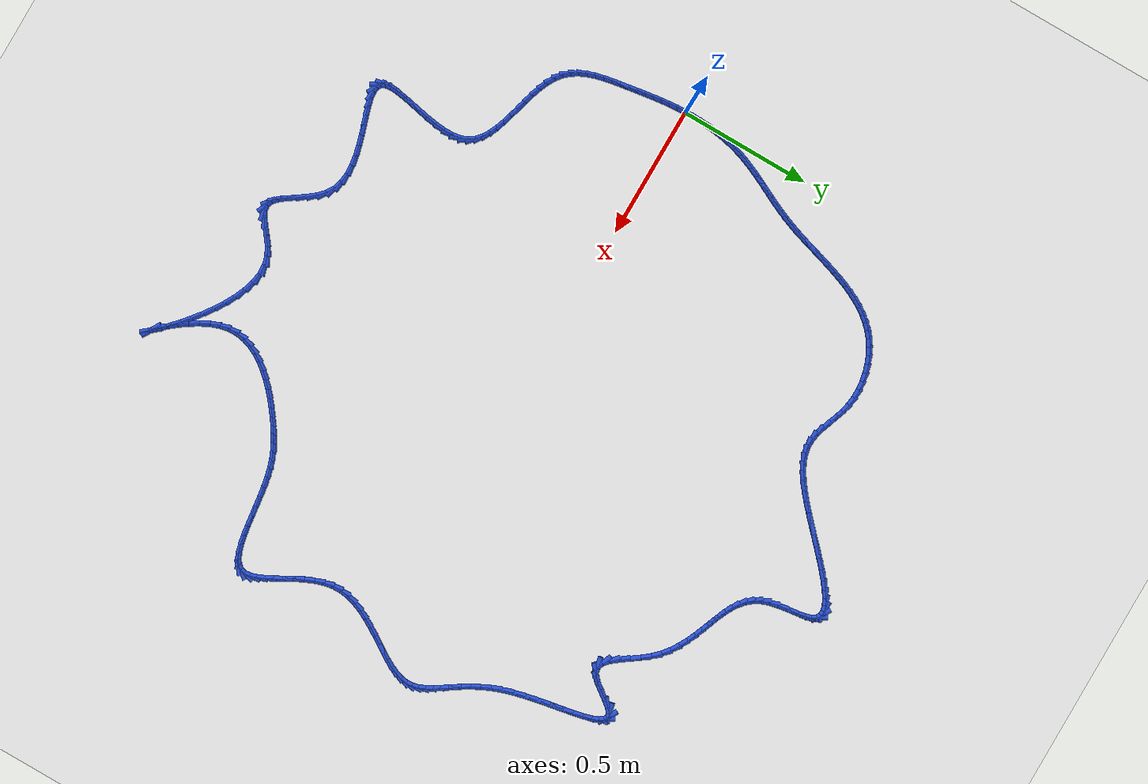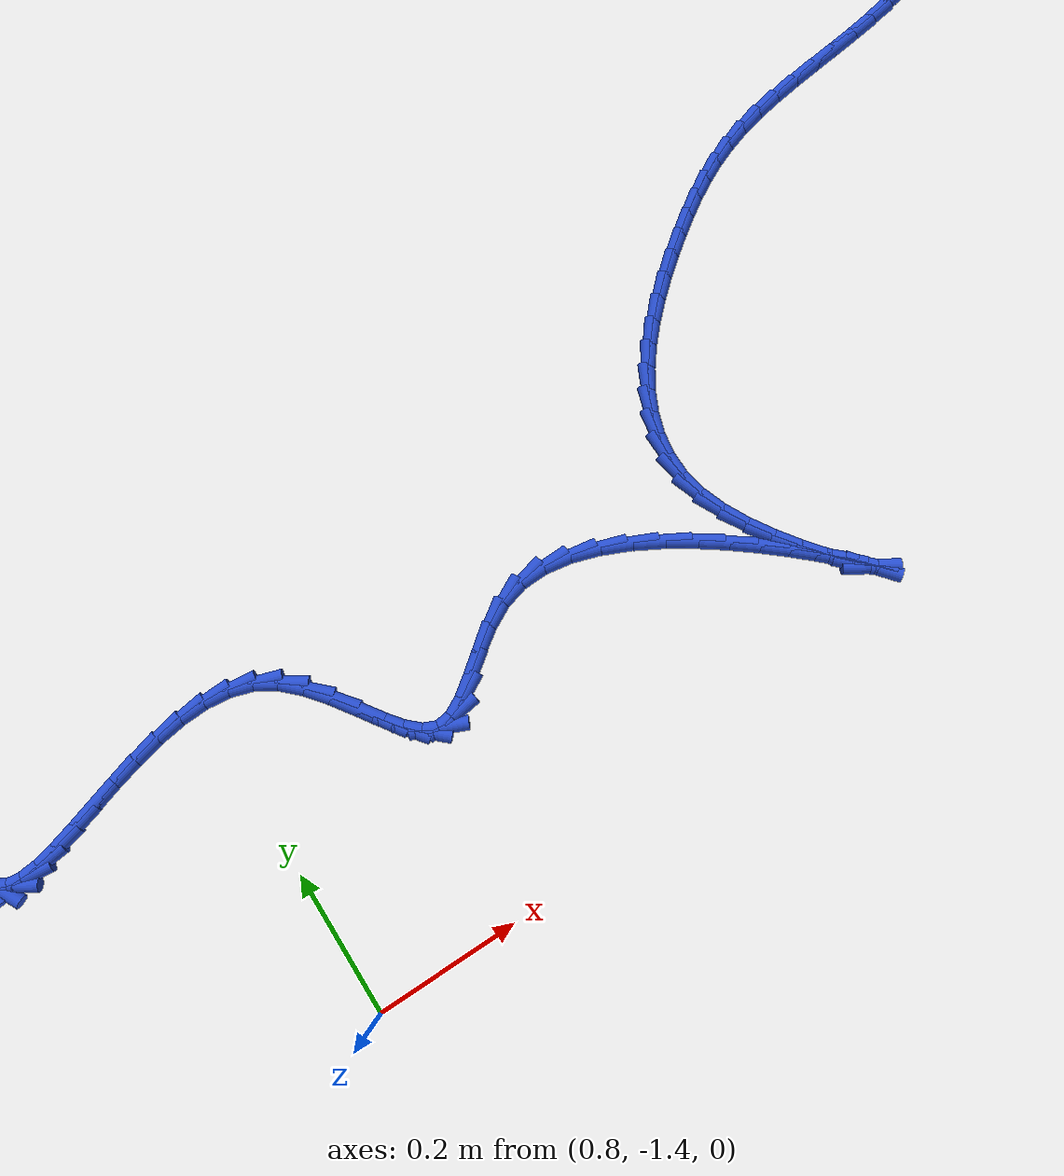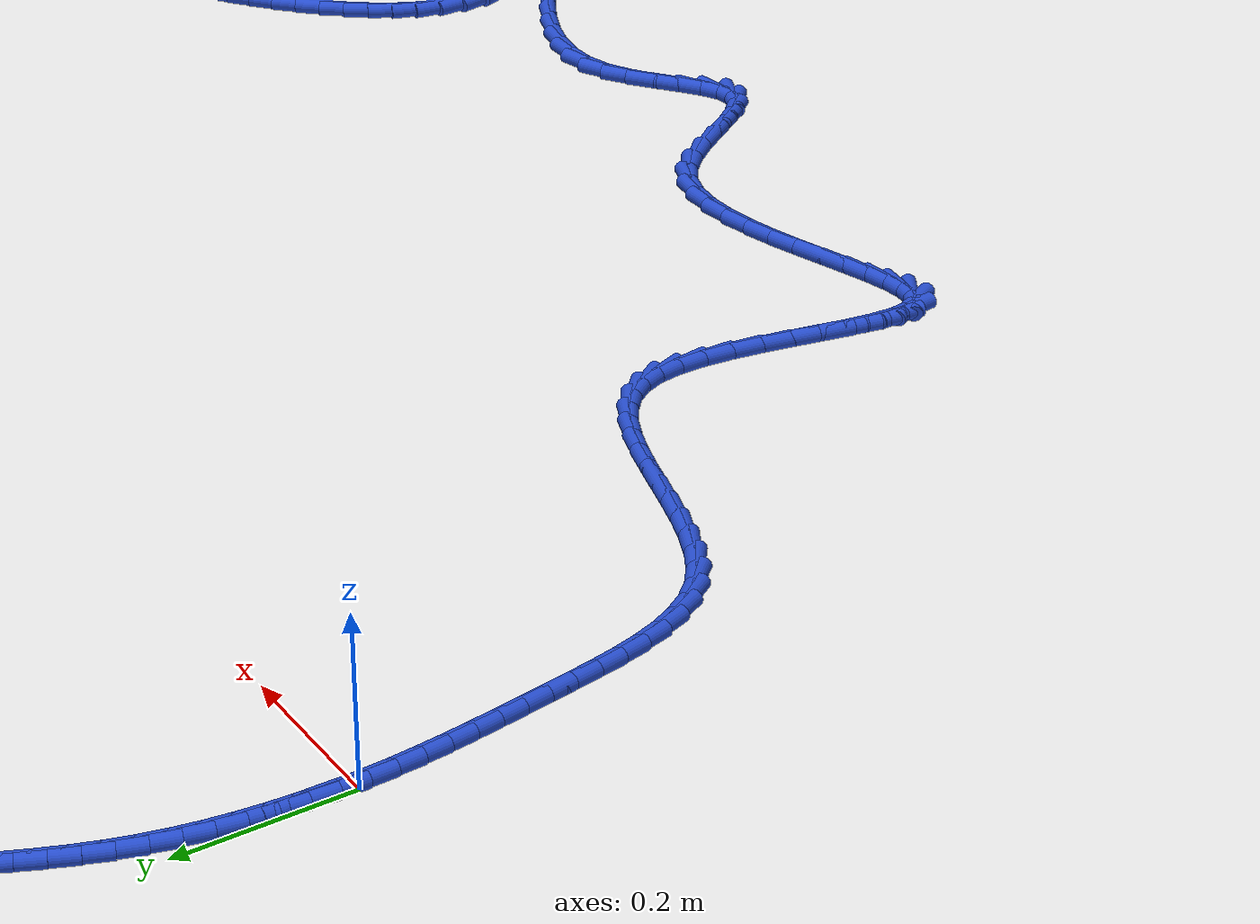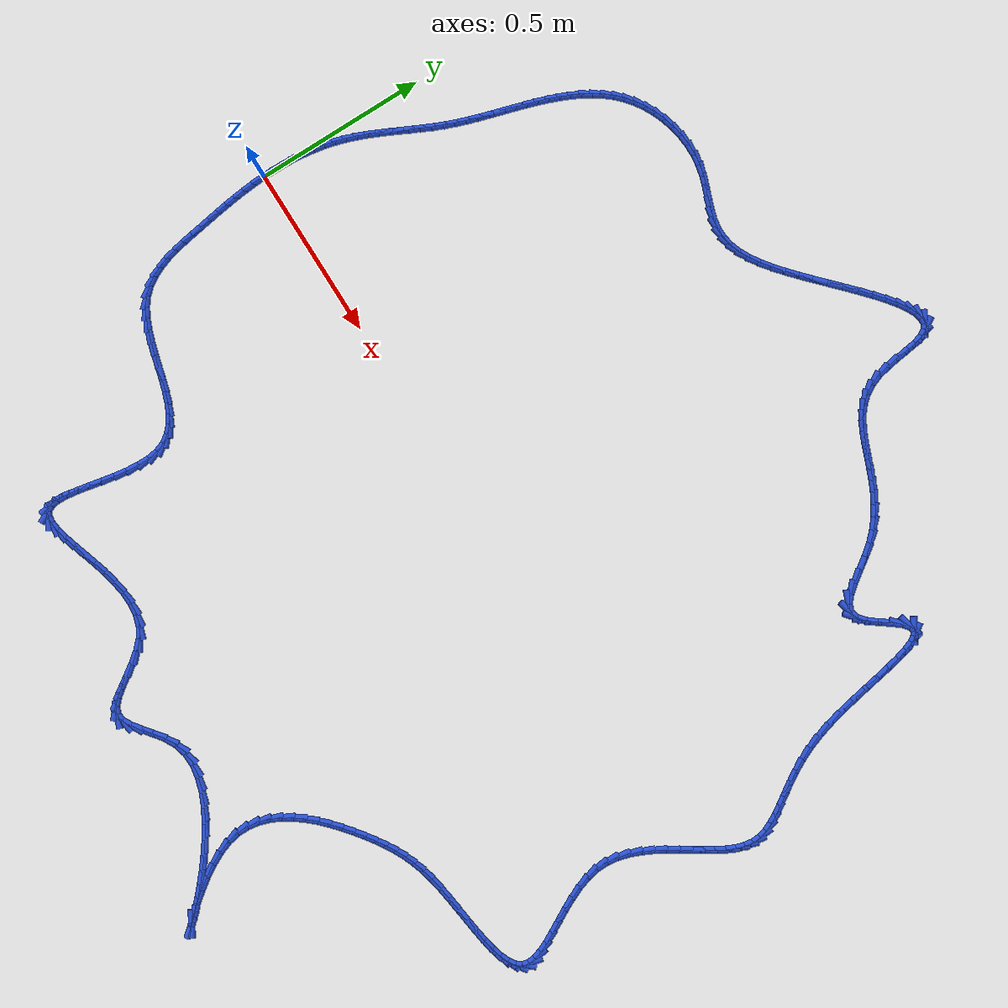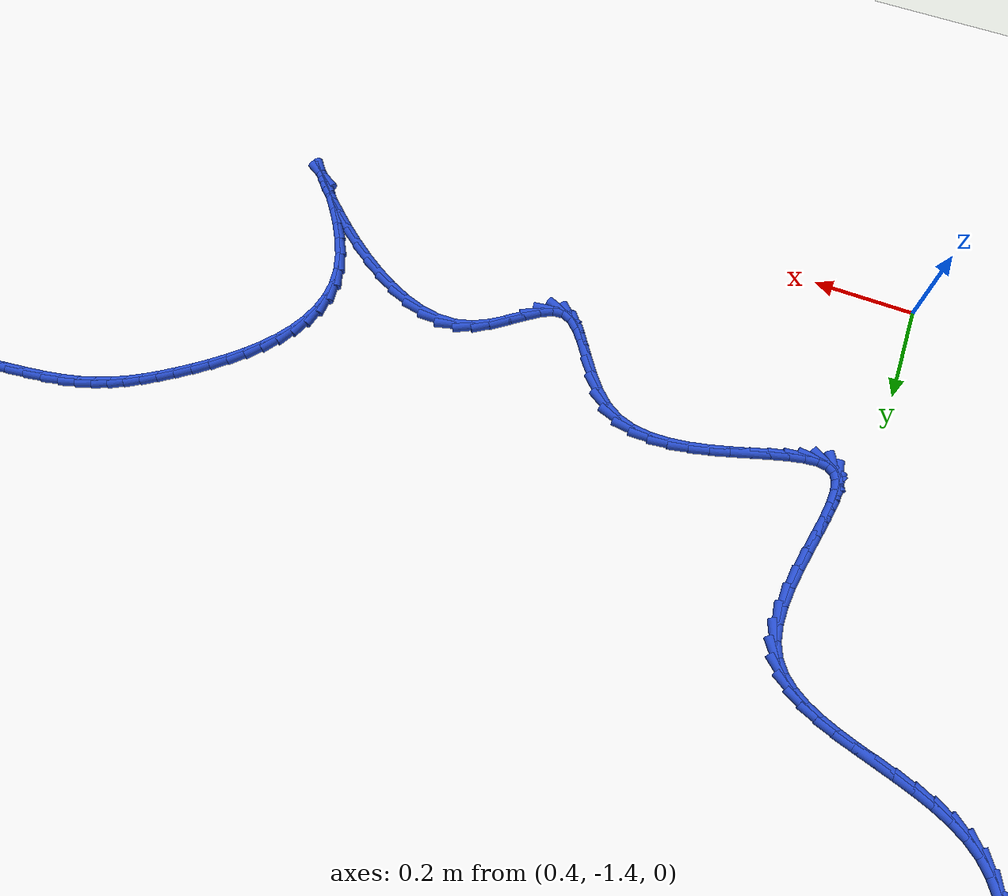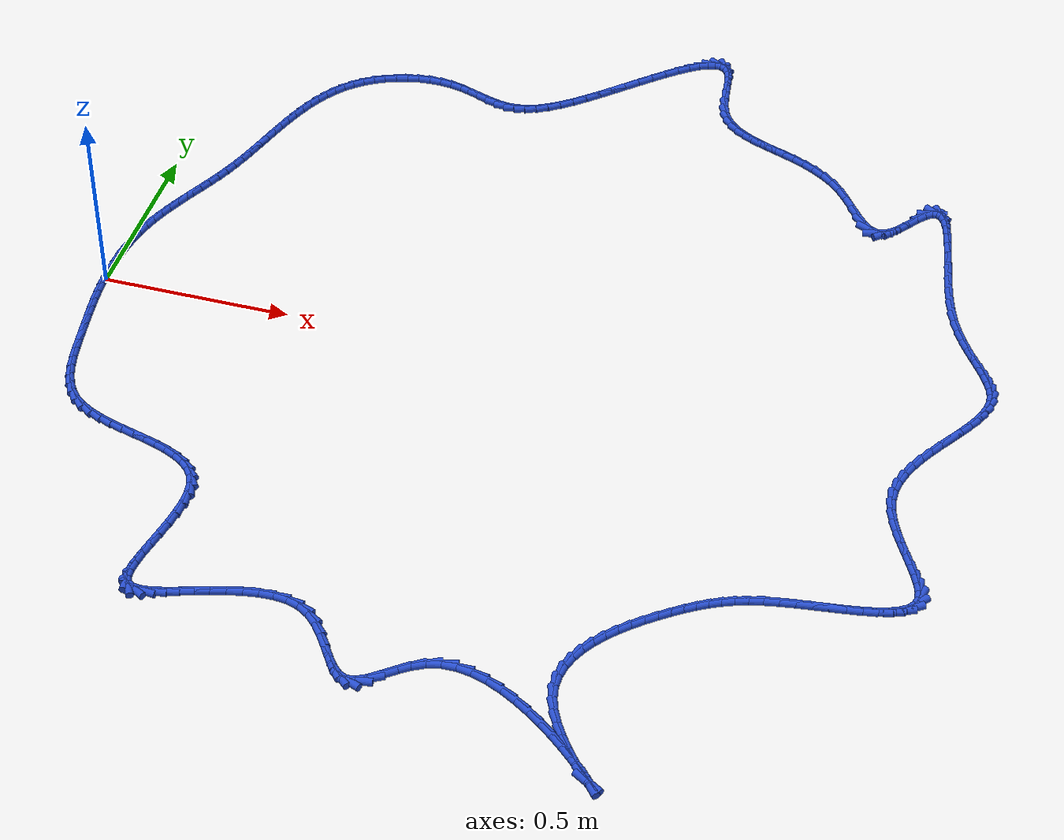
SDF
<sdf version="1.6">
 <world name="default">
  <light name="sun" type="directional">
   <pose>0 0 10 0 -0 0</pose>
   <diffuse>0.8 0.8 0.8 1</diffuse>
   <specular>0.2 0.2 0.2 1</specular>
   <attenuation>
    <range>1000</range>
    <constant>0.9</constant>
    <linear>0.01</linear>
    <quadratic>0.001</quadratic>
   </attenuation>
   <direction>-0.5 0.1 -0.9</direction>
  </light>
  <model name="ground_plane">
   <static>1</static>
   <link name="link">
    <collision name="collision">
     <geometry><plane><normal>0 0 1</normal><size>100 100</size></plane></geometry>
     <surface><friction><ode><mu>100</mu><mu2>50</mu2></ode></friction></surface>
    </collision>
    <visual name="visual">
     <cast_shadows>0</cast_shadows>
     <geometry><plane><normal>0 0 1</normal><size>100 100</size></plane></geometry>
     <material>
      <script><uri>file://media/materials/scripts/gazebo.material</uri><name>Gazebo/WhiteGlow</name></script>
     </material>
    </visual>
   </link>
  </model>
  <gravity>0 0 -9.8</gravity>
  <magnetic_field>6e-06 2.3e-05 -4.2e-05</magnetic_field>
  <atmosphere type="adiabatic"/>
  <physics name="default_physics" default="0" type="ode">
   <max_step_size>0.001</max_step_size>
   <real_time_factor>1</real_time_factor>
   <real_time_update_rate>1000</real_time_update_rate>
  </physics>
  <scene><ambient>0.4 0.4 0.4 1</ambient><background>0.7 0.7 0.7 1</background><shadows>1</shadows></scene>
  <spherical_coordinates>
   <surface_model>EARTH_WGS84</surface_model>
   <latitude_deg>0</latitude_deg>
   <longitude_deg>0</longitude_deg>
   <elevation>0</elevation>
   <heading_deg>0</heading_deg>
  </spherical_coordinates>
  <model name="line">
   <link name="link_0">
    <pose>1.3010426069826053e-18 2.0816681711721685e-17 0.01 0 1.57 -1.5575038894447397</pose>
    <collision name="collision">
     <geometry><cylinder><radius>0.01</radius><length>0.08</length></cylinder></geometry>
    </collision>
    <visual name="visual">
     <material>
      <script><name>Gazebo/Blue</name><uri>file://media/materials/scripts/gazebo.material</uri></script>
     </material>
     <geometry><cylinder><radius>0.01</radius><length>0.08</length></cylinder></geometry>
    </visual>
   </link>
   <link name="link_1">
    <pose>-0.00041409959676044783 0.03115118744836307 0.01 0 1.57 1.5482590688084805</pose>
    <collision name="collision">
     <geometry><cylinder><radius>0.01</radius><length>0.08</length></cylinder></geometry>
    </collision>
    <visual name="visual">
     <material>
      <script><name>Gazebo/Blue</name><uri>file://media/materials/scripts/gazebo.material</uri></script>
     </material>
     <geometry><cylinder><radius>0.01</radius><length>0.08</length></cylinder></geometry>
    </visual>
   </link>
   <link name="link_2">
    <pose>0.00029278531470994506 0.06251104611577475 0.01 0 1.57 1.5103837322290365</pose>
    <collision name="collision">
     <geometry><cylinder><radius>0.01</radius><length>0.08</length></cylinder></geometry>
    </collision>
    <visual name="visual">
     <material>
      <script><name>Gazebo/Blue</name><uri>file://media/materials/scripts/gazebo.material</uri></script>
     </material>
     <geometry><cylinder><radius>0.01</radius><length>0.08</length></cylinder></geometry>
    </visual>
   </link>
   <link name="link_3">
    <pose>0.002193637149858419 0.09393725425375617 0.01 0 1.57 1.470092604356373</pose>
    <collision name="collision">
     <geometry><cylinder><radius>0.01</radius><length>0.08</length></cylinder></geometry>
    </collision>
    <visual name="visual">
     <material>
      <script><name>Gazebo/Blue</name><uri>file://media/materials/scripts/gazebo.material</uri></script>
     </material>
     <geometry><cylinder><radius>0.01</radius><length>0.08</length></cylinder></geometry>
    </visual>
   </link>
   <link name="link_4">
    <pose>0.00536143832413221 0.12528749011382834 0.01 0 1.57 1.427001211475625</pose>
    <collision name="collision">
     <geometry><cylinder><radius>0.01</radius><length>0.08</length></cylinder></geometry>
    </collision>
    <visual name="visual">
     <material>
      <script><name>Gazebo/Blue</name><uri>file://media/materials/scripts/gazebo.material</uri></script>
     </material>
     <geometry><cylinder><radius>0.01</radius><length>0.08</length></cylinder></geometry>
    </visual>
   </link>
   <link name="link_5">
    <pose>0.009869171252978554 0.1564194319475123 0.01 0 1.57 1.3807113794045376</pose>
    <collision name="collision">
     <geometry><cylinder><radius>0.01</radius><length>0.08</length></cylinder></geometry>
    </collision>
    <visual name="visual">
     <material>
      <script><name>Gazebo/Blue</name><uri>file://media/materials/scripts/gazebo.material</uri></script>
     </material>
     <geometry><cylinder><radius>0.01</radius><length>0.08</length></cylinder></geometry>
    </visual>
   </link>
   <link name="link_6">
    <pose>0.015789818351844693 0.18719075800632914 0.01 0 1.57 1.3308161689650584</pose>
    <collision name="collision">
     <geometry><cylinder><radius>0.01</radius><length>0.08</length></cylinder></geometry>
    </collision>
    <visual name="visual">
     <material>
      <script><name>Gazebo/Blue</name><uri>file://media/materials/scripts/gazebo.material</uri></script>
     </material>
     <geometry><cylinder><radius>0.01</radius><length>0.08</length></cylinder></geometry>
    </visual>
   </link>
   <link name="link_7">
    <pose>0.023196362036177864 0.2174591465417999 0.01 0 1.57 1.2772878808390065</pose>
    <collision name="collision">
     <geometry><cylinder><radius>0.01</radius><length>0.08</length></cylinder></geometry>
    </collision>
    <visual name="visual">
     <material>
      <script><name>Gazebo/Blue</name><uri>file://media/materials/scripts/gazebo.material</uri></script>
     </material>
     <geometry><cylinder><radius>0.01</radius><length>0.08</length></cylinder></geometry>
    </visual>
   </link>
   <link name="link_8">
    <pose>0.032152131485604675 0.2470906916014249 0.01 0 1.57 1.2266485279615884</pose>
    <collision name="collision">
     <geometry><cylinder><radius>0.01</radius><length>0.08</length></cylinder></geometry>
    </collision>
    <visual name="visual">
     <material>
      <script><name>Gazebo/Blue</name><uri>file://media/materials/scripts/gazebo.material</uri></script>
     </material>
     <geometry><cylinder><radius>0.01</radius><length>0.08</length></cylinder></geometry>
    </visual>
   </link>
   <link name="link_9">
    <pose>0.04254954858058153 0.27610048607494714 0.01 0 1.57 1.185087152476926</pose>
    <collision name="collision">
     <geometry><cylinder><radius>0.01</radius><length>0.08</length></cylinder></geometry>
    </collision>
    <visual name="visual">
     <material>
      <script><name>Gazebo/Blue</name><uri>file://media/materials/scripts/gazebo.material</uri></script>
     </material>
     <geometry><cylinder><radius>0.01</radius><length>0.08</length></cylinder></geometry>
    </visual>
   </link>
   <link name="link_10">
    <pose>0.05413446693675658 0.30463140265947897 0.01 0 1.57 1.153146279682594</pose>
    <collision name="collision">
     <geometry><cylinder><radius>0.01</radius><length>0.08</length></cylinder></geometry>
    </collision>
    <visual name="visual">
     <material>
      <script><name>Gazebo/Blue</name><uri>file://media/materials/scripts/gazebo.material</uri></script>
     </material>
     <geometry><cylinder><radius>0.01</radius><length>0.08</length></cylinder></geometry>
    </visual>
   </link>
   <link name="link_11">
    <pose>0.06664799078491741 0.3328304546175097 0.01 0 1.57 1.1309513957985897</pose>
    <collision name="collision">
     <geometry><cylinder><radius>0.01</radius><length>0.08</length></cylinder></geometry>
    </collision>
    <visual name="visual">
     <material>
      <script><name>Gazebo/Blue</name><uri>file://media/materials/scripts/gazebo.material</uri></script>
     </material>
     <geometry><cylinder><radius>0.01</radius><length>0.08</length></cylinder></geometry>
    </visual>
   </link>
   <link name="link_12">
    <pose>0.0798312243558515 0.3608446552115284 0.01 0 1.57 1.1184825822149278</pose>
    <collision name="collision">
     <geometry><cylinder><radius>0.01</radius><length>0.08</length></cylinder></geometry>
    </collision>
    <visual name="visual">
     <material>
      <script><name>Gazebo/Blue</name><uri>file://media/materials/scripts/gazebo.material</uri></script>
     </material>
     <geometry><cylinder><radius>0.01</radius><length>0.08</length></cylinder></geometry>
    </visual>
   </link>
   <link name="link_13">
    <pose>0.09342527188034638 0.38882101770402433 0.01 0 1.57 1.1156386648064764</pose>
    <collision name="collision">
     <geometry><cylinder><radius>0.01</radius><length>0.08</length></cylinder></geometry>
    </collision>
    <visual name="visual">
     <material>
      <script><name>Gazebo/Blue</name><uri>file://media/materials/scripts/gazebo.material</uri></script>
     </material>
     <geometry><cylinder><radius>0.01</radius><length>0.08</length></cylinder></geometry>
    </visual>
   </link>
   <link name="link_14">
    <pose>0.10717123758918967 0.41690655535748705 0.01 0 1.57 1.122274312137525</pose>
    <collision name="collision">
     <geometry><cylinder><radius>0.01</radius><length>0.08</length></cylinder></geometry>
    </collision>
    <visual name="visual">
     <material>
      <script><name>Gazebo/Blue</name><uri>file://media/materials/scripts/gazebo.material</uri></script>
     </material>
     <geometry><cylinder><radius>0.01</radius><length>0.08</length></cylinder></geometry>
    </visual>
   </link>
   <link name="link_15">
    <pose>0.12081022571316884 0.4452482814344053 0.01 0 1.57 1.1382100350771376</pose>
    <collision name="collision">
     <geometry><cylinder><radius>0.01</radius><length>0.08</length></cylinder></geometry>
    </collision>
    <visual name="visual">
     <material>
      <script><name>Gazebo/Blue</name><uri>file://media/materials/scripts/gazebo.material</uri></script>
     </material>
     <geometry><cylinder><radius>0.01</radius><length>0.08</length></cylinder></geometry>
    </visual>
   </link>
   <link name="link_16">
    <pose>0.13408334048307144 0.4739932091972685 0.01 0 1.57 1.163217461635742</pose>
    <collision name="collision">
     <geometry><cylinder><radius>0.01</radius><length>0.08</length></cylinder></geometry>
    </collision>
    <visual name="visual">
     <material>
      <script><name>Gazebo/Blue</name><uri>file://media/materials/scripts/gazebo.material</uri></script>
     </material>
     <geometry><cylinder><radius>0.01</radius><length>0.08</length></cylinder></geometry>
    </visual>
   </link>
   <link name="link_17">
    <pose>0.146731686129685 0.5032883519085659 0.01 0 1.57 1.1965875367184091</pose>
    <collision name="collision">
     <geometry><cylinder><radius>0.01</radius><length>0.08</length></cylinder></geometry>
    </collision>
    <visual name="visual">
     <material>
      <script><name>Gazebo/Blue</name><uri>file://media/materials/scripts/gazebo.material</uri></script>
     </material>
     <geometry><cylinder><radius>0.01</radius><length>0.08</length></cylinder></geometry>
    </visual>
   </link>
   <link name="link_18">
    <pose>0.1585071708979973 0.5332733104056475 0.01 0 1.57 1.2295424686283842</pose>
    <collision name="collision">
     <geometry><cylinder><radius>0.01</radius><length>0.08</length></cylinder></geometry>
    </collision>
    <visual name="visual">
     <material>
      <script><name>Gazebo/Blue</name><uri>file://media/materials/scripts/gazebo.material</uri></script>
     </material>
     <geometry><cylinder><radius>0.01</radius><length>0.08</length></cylinder></geometry>
    </visual>
   </link>
   <link name="link_19">
    <pose>0.169394193767727 0.5639281781302972 0.01 0 1.57 1.2541638961549795</pose>
    <collision name="collision">
     <geometry><cylinder><radius>0.01</radius><length>0.08</length></cylinder></geometry>
    </collision>
    <visual name="visual">
     <material>
      <script><name>Gazebo/Blue</name><uri>file://media/materials/scripts/gazebo.material</uri></script>
     </material>
     <geometry><cylinder><radius>0.01</radius><length>0.08</length></cylinder></geometry>
    </visual>
   </link>
   <link name="link_20">
    <pose>0.1796010875475896 0.5950794118562224 0.01 0 1.57 1.2705048027986683</pose>
    <collision name="collision">
     <geometry><cylinder><radius>0.01</radius><length>0.08</length></cylinder></geometry>
    </collision>
    <visual name="visual">
     <material>
      <script><name>Gazebo/Blue</name><uri>file://media/materials/scripts/gazebo.material</uri></script>
     </material>
     <geometry><cylinder><radius>0.01</radius><length>0.08</length></cylinder></geometry>
    </visual>
   </link>
   <link name="link_21">
    <pose>0.18934527692489478 0.6265472305951106 0.01 0 1.57 1.2788309504073365</pose>
    <collision name="collision">
     <geometry><cylinder><radius>0.01</radius><length>0.08</length></cylinder></geometry>
    </collision>
    <visual name="visual">
     <material>
      <script><name>Gazebo/Blue</name><uri>file://media/materials/scripts/gazebo.material</uri></script>
     </material>
     <geometry><cylinder><radius>0.01</radius><length>0.08</length></cylinder></geometry>
    </visual>
   </link>
   <link name="link_22">
    <pose>0.19884418658695197 0.6581518533586487 0.01 0 1.57 1.2792650941294827</pose>
    <collision name="collision">
     <geometry><cylinder><radius>0.01</radius><length>0.08</length></cylinder></geometry>
    </collision>
    <visual name="visual">
     <material>
      <script><name>Gazebo/Blue</name><uri>file://media/materials/scripts/gazebo.material</uri></script>
     </material>
     <geometry><cylinder><radius>0.01</radius><length>0.08</length></cylinder></geometry>
    </visual>
   </link>
   <link name="link_23">
    <pose>0.20831524122107073 0.6897134991585232 0.01 0 1.57 1.2717760065190185</pose>
    <collision name="collision">
     <geometry><cylinder><radius>0.01</radius><length>0.08</length></cylinder></geometry>
    </collision>
    <visual name="visual">
     <material>
      <script><name>Gazebo/Blue</name><uri>file://media/materials/scripts/gazebo.material</uri></script>
     </material>
     <geometry><cylinder><radius>0.01</radius><length>0.08</length></cylinder></geometry>
    </visual>
   </link>
   <link name="link_24">
    <pose>0.21797586551456063 0.721052387006422 0.01 0 1.57 1.2561754801505745</pose>
    <collision name="collision">
     <geometry><cylinder><radius>0.01</radius><length>0.08</length></cylinder></geometry>
    </collision>
    <visual name="visual">
     <material>
      <script><name>Gazebo/Blue</name><uri>file://media/materials/scripts/gazebo.material</uri></script>
     </material>
     <geometry><cylinder><radius>0.01</radius><length>0.08</length></cylinder></geometry>
    </visual>
   </link>
   <link name="link_25">
    <pose>0.22804348415473125 0.7519887359140317 0.01 0 1.57 1.2321234150519773</pose>
    <collision name="collision">
     <geometry><cylinder><radius>0.01</radius><length>0.08</length></cylinder></geometry>
    </collision>
    <visual name="visual">
     <material>
      <script><name>Gazebo/Blue</name><uri>file://media/materials/scripts/gazebo.material</uri></script>
     </material>
     <geometry><cylinder><radius>0.01</radius><length>0.08</length></cylinder></geometry>
    </visual>
   </link>
   <link name="link_26">
    <pose>0.2387355218288919 0.7823427648930387 0.01 0 1.57 1.1991447269757256</pose>
    <collision name="collision">
     <geometry><cylinder><radius>0.01</radius><length>0.08</length></cylinder></geometry>
    </collision>
    <visual name="visual">
     <material>
      <script><name>Gazebo/Blue</name><uri>file://media/materials/scripts/gazebo.material</uri></script>
     </material>
     <geometry><cylinder><radius>0.01</radius><length>0.08</length></cylinder></geometry>
    </visual>
   </link>
   <link name="link_27">
    <pose>0.25026940322435237 0.8119346929551308 0.01 0 1.57 1.1566658814537734</pose>
    <collision name="collision">
     <geometry><cylinder><radius>0.01</radius><length>0.08</length></cylinder></geometry>
    </collision>
    <visual name="visual">
     <material>
      <script><name>Gazebo/Blue</name><uri>file://media/materials/scripts/gazebo.material</uri></script>
     </material>
     <geometry><cylinder><radius>0.01</radius><length>0.08</length></cylinder></geometry>
    </visual>
   </link>
   <link name="link_28">
    <pose>0.2628625530284221 0.8405847391119945 0.01 0 1.57 1.1040831111078588</pose>
    <collision name="collision">
     <geometry><cylinder><radius>0.01</radius><length>0.08</length></cylinder></geometry>
    </collision>
    <visual name="visual">
     <material>
      <script><name>Gazebo/Blue</name><uri>file://media/materials/scripts/gazebo.material</uri></script>
     </material>
     <geometry><cylinder><radius>0.01</radius><length>0.08</length></cylinder></geometry>
    </visual>
   </link>
   <link name="link_29">
    <pose>0.27673239592841054 0.8681131223753169 0.01 0 1.57 1.0408772059907272</pose>
    <collision name="collision">
     <geometry><cylinder><radius>0.01</radius><length>0.08</length></cylinder></geometry>
    </collision>
    <visual name="visual">
     <material>
      <script><name>Gazebo/Blue</name><uri>file://media/materials/scripts/gazebo.material</uri></script>
     </material>
     <geometry><cylinder><radius>0.01</radius><length>0.08</length></cylinder></geometry>
    </visual>
   </link>
   <link name="link_30">
    <pose>0.2920963566116275 0.8943400617567853 0.01 0 1.57 0.9667870633385875</pose>
    <collision name="collision">
     <geometry><cylinder><radius>0.01</radius><length>0.08</length></cylinder></geometry>
    </collision>
    <visual name="visual">
     <material>
      <script><name>Gazebo/Blue</name><uri>file://media/materials/scripts/gazebo.material</uri></script>
     </material>
     <geometry><cylinder><radius>0.01</radius><length>0.08</length></cylinder></geometry>
    </visual>
   </link>
   <link name="link_31">
    <pose>0.3091718597653822 0.9190857762680864 0.01 0 1.57 0.8820388716126148</pose>
    <collision name="collision">
     <geometry><cylinder><radius>0.01</radius><length>0.08</length></cylinder></geometry>
    </collision>
    <visual name="visual">
     <material>
      <script><name>Gazebo/Blue</name><uri>file://media/materials/scripts/gazebo.material</uri></script>
     </material>
     <geometry><cylinder><radius>0.01</radius><length>0.08</length></cylinder></geometry>
    </visual>
   </link>
   <link name="link_32">
    <pose>0.32817633007698443 0.9421704849209072 0.01 0 1.57 0.7875932329580316</pose>
    <collision name="collision">
     <geometry><cylinder><radius>0.01</radius><length>0.08</length></cylinder></geometry>
    </collision>
    <visual name="visual">
     <material>
      <script><name>Gazebo/Blue</name><uri>file://media/materials/scripts/gazebo.material</uri></script>
     </material>
     <geometry><cylinder><radius>0.01</radius><length>0.08</length></cylinder></geometry>
    </visual>
   </link>
   <link name="link_33">
    <pose>0.34932719223374353 0.9634144067269346 0.01 0 1.57 0.6853426953823873</pose>
    <collision name="collision">
     <geometry><cylinder><radius>0.01</radius><length>0.08</length></cylinder></geometry>
    </collision>
    <visual name="visual">
     <material>
      <script><name>Gazebo/Blue</name><uri>file://media/materials/scripts/gazebo.material</uri></script>
     </material>
     <geometry><cylinder><radius>0.01</radius><length>0.08</length></cylinder></geometry>
    </visual>
   </link>
   <link name="link_34">
    <pose>0.372840938359978 0.982637746894926 0.01 0 1.57 0.5810526060741649</pose>
    <collision name="collision">
     <geometry><cylinder><radius>0.01</radius><length>0.08</length></cylinder></geometry>
    </collision>
    <visual name="visual">
     <material>
      <script><name>Gazebo/Blue</name><uri>file://media/materials/scripts/gazebo.material</uri></script>
     </material>
     <geometry><cylinder><radius>0.01</radius><length>0.08</length></cylinder></geometry>
    </visual>
   </link>
   <link name="link_35">
    <pose>0.3987600243658531 0.9996581347115356 0.01 0 1.57 0.48162295023544005</pose>
    <collision name="collision">
     <geometry><cylinder><radius>0.01</radius><length>0.08</length></cylinder></geometry>
    </collision>
    <visual name="visual">
     <material>
      <script><name>Gazebo/Blue</name><uri>file://media/materials/scripts/gazebo.material</uri></script>
     </material>
     <geometry><cylinder><radius>0.01</radius><length>0.08</length></cylinder></geometry>
    </visual>
   </link>
   <link name="link_36">
    <pose>0.42674963361512547 1.0142876154262326 0.01 0 1.57 0.3857102588434882</pose>
    <collision name="collision">
     <geometry><cylinder><radius>0.01</radius><length>0.08</length></cylinder></geometry>
    </collision>
    <visual name="visual">
     <material>
      <script><name>Gazebo/Blue</name><uri>file://media/materials/scripts/gazebo.material</uri></script>
     </material>
     <geometry><cylinder><radius>0.01</radius><length>0.08</length></cylinder></geometry>
    </visual>
   </link>
   <link name="link_37">
    <pose>0.45642556815300156 1.0263375033921582 0.01 0 1.57 0.2911070284629027</pose>
    <collision name="collision">
     <geometry><cylinder><radius>0.01</radius><length>0.08</length></cylinder></geometry>
    </collision>
    <visual name="visual">
     <material>
      <script><name>Gazebo/Blue</name><uri>file://media/materials/scripts/gazebo.material</uri></script>
     </material>
     <geometry><cylinder><radius>0.01</radius><length>0.08</length></cylinder></geometry>
    </visual>
   </link>
   <link name="link_38">
    <pose>0.48740363002468773 1.0356191129624528 0.01 0 1.57 0.19575047061418677</pose>
    <collision name="collision">
     <geometry><cylinder><radius>0.01</radius><length>0.08</length></cylinder></geometry>
    </collision>
    <visual name="visual">
     <material>
      <script><name>Gazebo/Blue</name><uri>file://media/materials/scripts/gazebo.material</uri></script>
     </material>
     <geometry><cylinder><radius>0.01</radius><length>0.08</length></cylinder></geometry>
    </visual>
   </link>
   <link name="link_39">
    <pose>0.5192996212753912 1.0419437584902573 0.01 0 1.57 0.09771503438905982</pose>
    <collision name="collision">
     <geometry><cylinder><radius>0.01</radius><length>0.08</length></cylinder></geometry>
    </collision>
    <visual name="visual">
     <material>
      <script><name>Gazebo/Blue</name><uri>file://media/materials/scripts/gazebo.material</uri></script>
     </material>
     <geometry><cylinder><radius>0.01</radius><length>0.08</length></cylinder></geometry>
    </visual>
   </link>
   <link name="link_40">
    <pose>0.5517293439503183 1.0451227543287132 0.01 0 1.57 -0.004768013115533468</pose>
    <collision name="collision">
     <geometry><cylinder><radius>0.01</radius><length>0.08</length></cylinder></geometry>
    </collision>
    <visual name="visual">
     <material>
      <script><name>Gazebo/Blue</name><uri>file://media/materials/scripts/gazebo.material</uri></script>
     </material>
     <geometry><cylinder><radius>0.01</radius><length>0.08</length></cylinder></geometry>
    </visual>
   </link>
   <link name="link_41">
    <pose>0.5843086000946759 1.0449674148309607 0.01 0 1.57 -0.11323762619417058</pose>
    <collision name="collision">
     <geometry><cylinder><radius>0.01</radius><length>0.08</length></cylinder></geometry>
    </collision>
    <visual name="visual">
     <material>
      <script><name>Gazebo/Blue</name><uri>file://media/materials/scripts/gazebo.material</uri></script>
     </material>
     <geometry><cylinder><radius>0.01</radius><length>0.08</length></cylinder></geometry>
    </visual>
   </link>
   <link name="link_42">
    <pose>0.6166531917536708 1.0412890543501414 0.01 0 1.57 -0.22597381143919948</pose>
    <collision name="collision">
     <geometry><cylinder><radius>0.01</radius><length>0.08</length></cylinder></geometry>
    </collision>
    <visual name="visual">
     <material>
      <script><name>Gazebo/Blue</name><uri>file://media/materials/scripts/gazebo.material</uri></script>
     </material>
     <geometry><cylinder><radius>0.01</radius><length>0.08</length></cylinder></geometry>
    </visual>
   </link>
   <link name="link_43">
    <pose>0.6483998674388132 1.0339904801967965 0.01 0 1.57 -0.31101951139018374</pose>
    <collision name="collision">
     <geometry><cylinder><radius>0.01</radius><length>0.08</length></cylinder></geometry>
    </collision>
    <visual name="visual">
     <material>
      <script><name>Gazebo/Blue</name><uri>file://media/materials/scripts/gazebo.material</uri></script>
     </material>
     <geometry><cylinder><radius>0.01</radius><length>0.08</length></cylinder></geometry>
    </visual>
   </link>
   <link name="link_44">
    <pose>0.6794241948713509 1.024017648223401 0.01 0 1.57 -0.34902840243961847</pose>
    <collision name="collision">
     <geometry><cylinder><radius>0.01</radius><length>0.08</length></cylinder></geometry>
    </collision>
    <visual name="visual">
     <material>
      <script><name>Gazebo/Blue</name><uri>file://media/materials/scripts/gazebo.material</uri></script>
     </material>
     <geometry><cylinder><radius>0.01</radius><length>0.08</length></cylinder></geometry>
    </visual>
   </link>
   <link name="link_45">
    <pose>0.7097536235604166 1.0129799251770222 0.01 0 1.57 -0.3396768665185254</pose>
    <collision name="collision">
     <geometry><cylinder><radius>0.01</radius><length>0.08</length></cylinder></geometry>
    </collision>
    <visual name="visual">
     <material>
      <script><name>Gazebo/Blue</name><uri>file://media/materials/scripts/gazebo.material</uri></script>
     </material>
     <geometry><cylinder><radius>0.01</radius><length>0.08</length></cylinder></geometry>
    </visual>
   </link>
   <link name="link_46">
    <pose>0.73941803755924 1.0024973117530096 0.01 0 1.57 -0.27872707697941873</pose>
    <collision name="collision">
     <geometry><cylinder><radius>0.01</radius><length>0.08</length></cylinder></geometry>
    </collision>
    <visual name="visual">
     <material>
      <script><name>Gazebo/Blue</name><uri>file://media/materials/scripts/gazebo.material</uri></script>
     </material>
     <geometry><cylinder><radius>0.01</radius><length>0.08</length></cylinder></geometry>
    </visual>
   </link>
   <link name="link_47">
    <pose>0.7684473209210515 0.9941898086467134 0.01 0 1.57 -0.15743979384755247</pose>
    <collision name="collision">
     <geometry><cylinder><radius>0.01</radius><length>0.08</length></cylinder></geometry>
    </collision>
    <visual name="visual">
     <material>
      <script><name>Gazebo/Blue</name><uri>file://media/materials/scripts/gazebo.material</uri></script>
     </material>
     <geometry><cylinder><radius>0.01</radius><length>0.08</length></cylinder></geometry>
    </visual>
   </link>
   <link name="link_48">
    <pose>0.796871360530564 0.9896773883994754 0.01 0 1.57 0.01872770850836995</pose>
    <collision name="collision">
     <geometry><cylinder><radius>0.01</radius><length>0.08</length></cylinder></geometry>
    </collision>
    <visual name="visual">
     <material>
      <script><name>Gazebo/Blue</name><uri>file://media/materials/scripts/gazebo.material</uri></script>
     </material>
     <geometry><cylinder><radius>0.01</radius><length>0.08</length></cylinder></geometry>
    </visual>
   </link>
   <link name="link_49">
    <pose>0.8247582921056165 0.9901997077904828 0.01 0 1.57 0.19572246314309089</pose>
    <collision name="collision">
     <geometry><cylinder><radius>0.01</radius><length>0.08</length></cylinder></geometry>
    </collision>
    <visual name="visual">
     <material>
      <script><name>Gazebo/Blue</name><uri>file://media/materials/scripts/gazebo.material</uri></script>
     </material>
     <geometry><cylinder><radius>0.01</radius><length>0.08</length></cylinder></geometry>
    </visual>
   </link>
   <link name="link_50">
    <pose>0.8523104347957068 0.9956622110253481 0.01 0 1.57 0.34987194286308243</pose>
    <collision name="collision">
     <geometry><cylinder><radius>0.01</radius><length>0.08</length></cylinder></geometry>
    </collision>
    <visual name="visual">
     <material>
      <script><name>Gazebo/Blue</name><uri>file://media/materials/scripts/gazebo.material</uri></script>
     </material>
     <geometry><cylinder><radius>0.01</radius><length>0.08</length></cylinder></geometry>
    </visual>
   </link>
   <link name="link_51">
    <pose>0.8797595165468808 1.005677924791043 0.01 0 1.57 0.4749851984436684</pose>
    <collision name="collision">
     <geometry><cylinder><radius>0.01</radius><length>0.08</length></cylinder></geometry>
    </collision>
    <visual name="visual">
     <material>
      <script><name>Gazebo/Blue</name><uri>file://media/materials/scripts/gazebo.material</uri></script>
     </material>
     <geometry><cylinder><radius>0.01</radius><length>0.08</length></cylinder></geometry>
    </visual>
   </link>
   <link name="link_52">
    <pose>0.9073372653051858 1.0198598757745394 0.01 0 1.57 0.5713622906258419</pose>
    <collision name="collision">
     <geometry><cylinder><radius>0.01</radius><length>0.08</length></cylinder></geometry>
    </collision>
    <visual name="visual">
     <material>
      <script><name>Gazebo/Blue</name><uri>file://media/materials/scripts/gazebo.material</uri></script>
     </material>
     <geometry><cylinder><radius>0.01</radius><length>0.08</length></cylinder></geometry>
    </visual>
   </link>
   <link name="link_53">
    <pose>0.9352754090166673 1.0378210906628087 0.01 0 1.57 0.6425089868736221</pose>
    <collision name="collision">
     <geometry><cylinder><radius>0.01</radius><length>0.08</length></cylinder></geometry>
    </collision>
    <visual name="visual">
     <material>
      <script><name>Gazebo/Blue</name><uri>file://media/materials/scripts/gazebo.material</uri></script>
     </material>
     <geometry><cylinder><radius>0.01</radius><length>0.08</length></cylinder></geometry>
    </visual>
   </link>
   <link name="link_54">
    <pose>0.9638056756273718 1.0591745961428223 0.01 0 1.57 0.6926650609308639</pose>
    <collision name="collision">
     <geometry><cylinder><radius>0.01</radius><length>0.08</length></cylinder></geometry>
    </collision>
    <visual name="visual">
     <material>
      <script><name>Gazebo/Blue</name><uri>file://media/materials/scripts/gazebo.material</uri></script>
     </material>
     <geometry><cylinder><radius>0.01</radius><length>0.08</length></cylinder></geometry>
    </visual>
   </link>
   <link name="link_55">
    <pose>0.9931597930833457 1.0835334189015522 0.01 0 1.57 0.7257654783107281</pose>
    <collision name="collision">
     <geometry><cylinder><radius>0.01</radius><length>0.08</length></cylinder></geometry>
    </collision>
    <visual name="visual">
     <material>
      <script><name>Gazebo/Blue</name><uri>file://media/materials/scripts/gazebo.material</uri></script>
     </material>
     <geometry><cylinder><radius>0.01</radius><length>0.08</length></cylinder></geometry>
    </visual>
   </link>
   <link name="link_56">
    <pose>1.023509365200127 1.1104632139518917 0.01 0 1.57 0.7458977917200066</pose>
    <collision name="collision">
     <geometry><cylinder><radius>0.01</radius><length>0.08</length></cylinder></geometry>
    </collision>
    <visual name="visual">
     <material>
      <script><name>Gazebo/Blue</name><uri>file://media/materials/scripts/gazebo.material</uri></script>
     </material>
     <geometry><cylinder><radius>0.01</radius><length>0.08</length></cylinder></geometry>
    </visual>
   </link>
   <link name="link_57">
    <pose>1.054630714018377 1.1392181946401305 0.01 0 1.57 0.7559839830697123</pose>
    <collision name="collision">
     <geometry><cylinder><radius>0.01</radius><length>0.08</length></cylinder></geometry>
    </collision>
    <visual name="visual">
     <material>
      <script><name>Gazebo/Blue</name><uri>file://media/materials/scripts/gazebo.material</uri></script>
     </material>
     <geometry><cylinder><radius>0.01</radius><length>0.08</length></cylinder></geometry>
    </visual>
   </link>
   <link name="link_58">
    <pose>1.086140526977499 1.1689267985510052 0.01 0 1.57 0.7572804624513156</pose>
    <collision name="collision">
     <geometry><cylinder><radius>0.01</radius><length>0.08</length></cylinder></geometry>
    </collision>
    <visual name="visual">
     <material>
      <script><name>Gazebo/Blue</name><uri>file://media/materials/scripts/gazebo.material</uri></script>
     </material>
     <geometry><cylinder><radius>0.01</radius><length>0.08</length></cylinder></geometry>
    </visual>
   </link>
   <link name="link_59">
    <pose>1.1176550462431876 1.1987171124390479 0.01 0 1.57 0.7499040288163119</pose>
    <collision name="collision">
     <geometry><cylinder><radius>0.01</radius><length>0.08</length></cylinder></geometry>
    </collision>
    <visual name="visual">
     <material>
      <script><name>Gazebo/Blue</name><uri>file://media/materials/scripts/gazebo.material</uri></script>
     </material>
     <geometry><cylinder><radius>0.01</radius><length>0.08</length></cylinder></geometry>
    </visual>
   </link>
   <link name="link_60">
    <pose>1.148790513981138 1.2277172230587903 0.01 0 1.57 0.7328624229318897</pose>
    <collision name="collision">
     <geometry><cylinder><radius>0.01</radius><length>0.08</length></cylinder></geometry>
    </collision>
    <visual name="visual">
     <material>
      <script><name>Gazebo/Blue</name><uri>file://media/materials/scripts/gazebo.material</uri></script>
     </material>
     <geometry><cylinder><radius>0.01</radius><length>0.08</length></cylinder></geometry>
    </visual>
   </link>
   <link name="link_61">
    <pose>1.1791631723570435 1.255055217164764 0.01 0 1.57 0.7037345023651381</pose>
    <collision name="collision">
     <geometry><cylinder><radius>0.01</radius><length>0.08</length></cylinder></geometry>
    </collision>
    <visual name="visual">
     <material>
      <script><name>Gazebo/Blue</name><uri>file://media/materials/scripts/gazebo.material</uri></script>
     </material>
     <geometry><cylinder><radius>0.01</radius><length>0.08</length></cylinder></geometry>
    </visual>
   </link>
   <link name="link_62">
    <pose>1.2083892635366 1.2798591815115017 0.01 0 1.57 0.6578150701129689</pose>
    <collision name="collision">
     <geometry><cylinder><radius>0.01</radius><length>0.08</length></cylinder></geometry>
    </collision>
    <visual name="visual">
     <material>
      <script><name>Gazebo/Blue</name><uri>file://media/materials/scripts/gazebo.material</uri></script>
     </material>
     <geometry><cylinder><radius>0.01</radius><length>0.08</length></cylinder></geometry>
    </visual>
   </link>
   <link name="link_63">
    <pose>1.2360850296855024 1.3012572028535354 0.01 0 1.57 0.5861845242551736</pose>
    <collision name="collision">
     <geometry><cylinder><radius>0.01</radius><length>0.08</length></cylinder></geometry>
    </collision>
    <visual name="visual">
     <material>
      <script><name>Gazebo/Blue</name><uri>file://media/materials/scripts/gazebo.material</uri></script>
     </material>
     <geometry><cylinder><radius>0.01</radius><length>0.08</length></cylinder></geometry>
    </visual>
   </link>
   <link name="link_64">
    <pose>1.2618667129694452 1.318377367945397 0.01 0 1.57 0.47140048195691125</pose>
    <collision name="collision">
     <geometry><cylinder><radius>0.01</radius><length>0.08</length></cylinder></geometry>
    </collision>
    <visual name="visual">
     <material>
      <script><name>Gazebo/Blue</name><uri>file://media/materials/scripts/gazebo.material</uri></script>
     </material>
     <geometry><cylinder><radius>0.01</radius><length>0.08</length></cylinder></geometry>
    </visual>
   </link>
   <link name="link_65">
    <pose>1.2853505555541223 1.3303477635416179 0.01 0 1.57 0.27853139766702234</pose>
    <collision name="collision">
     <geometry><cylinder><radius>0.01</radius><length>0.08</length></cylinder></geometry>
    </collision>
    <visual name="visual">
     <material>
      <script><name>Gazebo/Blue</name><uri>file://media/materials/scripts/gazebo.material</uri></script>
     </material>
     <geometry><cylinder><radius>0.01</radius><length>0.08</length></cylinder></geometry>
    </visual>
   </link>
   <link name="link_66">
    <pose>1.3061527996052291 1.3362964763967307 0.01 0 1.57 -0.05322189723997047</pose>
    <collision name="collision">
     <geometry><cylinder><radius>0.01</radius><length>0.08</length></cylinder></geometry>
    </collision>
    <visual name="visual">
     <material>
      <script><name>Gazebo/Blue</name><uri>file://media/materials/scripts/gazebo.material</uri></script>
     </material>
     <geometry><cylinder><radius>0.01</radius><length>0.08</length></cylinder></geometry>
    </visual>
   </link>
   <link name="link_67">
    <pose>1.3238896872884598 1.3353515932652669 0.01 0 1.57 -0.547477301090265</pose>
    <collision name="collision">
     <geometry><cylinder><radius>0.01</radius><length>0.08</length></cylinder></geometry>
    </collision>
    <visual name="visual">
     <material>
      <script><name>Gazebo/Blue</name><uri>file://media/materials/scripts/gazebo.material</uri></script>
     </material>
     <geometry><cylinder><radius>0.01</radius><length>0.08</length></cylinder></geometry>
    </visual>
   </link>
   <link name="link_68">
    <pose>1.3381774607695103 1.3266412009017596 0.01 0 1.57 -1.0251447185116218</pose>
    <collision name="collision">
     <geometry><cylinder><radius>0.01</radius><length>0.08</length></cylinder></geometry>
    </collision>
    <visual name="visual">
     <material>
      <script><name>Gazebo/Blue</name><uri>file://media/materials/scripts/gazebo.material</uri></script>
     </material>
     <geometry><cylinder><radius>0.01</radius><length>0.08</length></cylinder></geometry>
    </visual>
   </link>
   <link name="link_69">
    <pose>1.3486690461316018 1.3093608084153763 0.01 0 1.57 -1.2921160792339452</pose>
    <collision name="collision">
     <geometry><cylinder><radius>0.01</radius><length>0.08</length></cylinder></geometry>
    </collision>
    <visual name="visual">
     <material>
      <script><name>Gazebo/Blue</name><uri>file://media/materials/scripts/gazebo.material</uri></script>
     </material>
     <geometry><cylinder><radius>0.01</radius><length>0.08</length></cylinder></geometry>
    </visual>
   </link>
   <link name="link_70">
    <pose>1.355855136973155 1.2842456802718472 0.01 0 1.57 -1.4027228436416574</pose>
    <collision name="collision">
     <geometry><cylinder><radius>0.01</radius><length>0.08</length></cylinder></geometry>
    </collision>
    <visual name="visual">
     <material>
      <script><name>Gazebo/Blue</name><uri>file://media/materials/scripts/gazebo.material</uri></script>
     </material>
     <geometry><cylinder><radius>0.01</radius><length>0.08</length></cylinder></geometry>
    </visual>
   </link>
   <link name="link_71">
    <pose>1.361060895187166 1.2535647725675039 0.01 0 1.57 -1.4363598154307848</pose>
    <collision name="collision">
     <geometry><cylinder><radius>0.01</radius><length>0.08</length></cylinder></geometry>
    </collision>
    <visual name="visual">
     <material>
      <script><name>Gazebo/Blue</name><uri>file://media/materials/scripts/gazebo.material</uri></script>
     </material>
     <geometry><cylinder><radius>0.01</radius><length>0.08</length></cylinder></geometry>
    </visual>
   </link>
   <link name="link_72">
    <pose>1.3656475067368106 1.2196532510022042 0.01 0 1.57 -1.4188842971220965</pose>
    <collision name="collision">
     <geometry><cylinder><radius>0.01</radius><length>0.08</length></cylinder></geometry>
    </collision>
    <visual name="visual">
     <material>
      <script><name>Gazebo/Blue</name><uri>file://media/materials/scripts/gazebo.material</uri></script>
     </material>
     <geometry><cylinder><radius>0.01</radius><length>0.08</length></cylinder></geometry>
    </visual>
   </link>
   <link name="link_73">
    <pose>1.370976157585267 1.1848462812758067 0.01 0 1.57 -1.3516438923917342</pose>
    <collision name="collision">
     <geometry><cylinder><radius>0.01</radius><length>0.08</length></cylinder></geometry>
    </collision>
    <visual name="visual">
     <material>
      <script><name>Gazebo/Blue</name><uri>file://media/materials/scripts/gazebo.material</uri></script>
     </material>
     <geometry><cylinder><radius>0.01</radius><length>0.08</length></cylinder></geometry>
    </visual>
   </link>
   <link name="link_74">
    <pose>1.378408033695712 1.1514790290881702 0.01 0 1.57 -1.2197613411176336</pose>
    <collision name="collision">
     <geometry><cylinder><radius>0.01</radius><length>0.08</length></cylinder></geometry>
    </collision>
    <visual name="visual">
     <material>
      <script><name>Gazebo/Blue</name><uri>file://media/materials/scripts/gazebo.material</uri></script>
     </material>
     <geometry><cylinder><radius>0.01</radius><length>0.08</length></cylinder></geometry>
    </visual>
   </link>
   <link name="link_75">
    <pose>1.3892674923155086 1.12182473006647 0.01 0 1.57 -1.0394744714232016</pose>
    <collision name="collision">
     <geometry><cylinder><radius>0.01</radius><length>0.08</length></cylinder></geometry>
    </collision>
    <visual name="visual">
     <material>
      <script><name>Gazebo/Blue</name><uri>file://media/materials/scripts/gazebo.material</uri></script>
     </material>
     <geometry><cylinder><radius>0.01</radius><length>0.08</length></cylinder></geometry>
    </visual>
   </link>
   <link name="link_76">
    <pose>1.4040229660546213 1.0967173224355287 0.01 0 1.57 -0.8591904363915909</pose>
    <collision name="collision">
     <geometry><cylinder><radius>0.01</radius><length>0.08</length></cylinder></geometry>
    </collision>
    <visual name="visual">
     <material>
      <script><name>Gazebo/Blue</name><uri>file://media/materials/scripts/gazebo.material</uri></script>
     </material>
     <geometry><cylinder><radius>0.01</radius><length>0.08</length></cylinder></geometry>
    </visual>
   </link>
   <link name="link_77">
    <pose>1.4222820091883694 1.0755431170279126 0.01 0 1.57 -0.6986355467073119</pose>
    <collision name="collision">
     <geometry><cylinder><radius>0.01</radius><length>0.08</length></cylinder></geometry>
    </collision>
    <visual name="visual">
     <material>
      <script><name>Gazebo/Blue</name><uri>file://media/materials/scripts/gazebo.material</uri></script>
     </material>
     <geometry><cylinder><radius>0.01</radius><length>0.08</length></cylinder></geometry>
    </visual>
   </link>
   <link name="link_78">
    <pose>1.443614356526461 1.0576248285881331 0.01 0 1.57 -0.5691773472983183</pose>
    <collision name="collision">
     <geometry><cylinder><radius>0.01</radius><length>0.08</length></cylinder></geometry>
    </collision>
    <visual name="visual">
     <material>
      <script><name>Gazebo/Blue</name><uri>file://media/materials/scripts/gazebo.material</uri></script>
     </material>
     <geometry><cylinder><radius>0.01</radius><length>0.08</length></cylinder></geometry>
    </visual>
   </link>
   <link name="link_79">
    <pose>1.4675897428786069 1.0422851718607025 0.01 0 1.57 -0.4741078250498231</pose>
    <collision name="collision">
     <geometry><cylinder><radius>0.01</radius><length>0.08</length></cylinder></geometry>
    </collision>
    <visual name="visual">
     <material>
      <script><name>Gazebo/Blue</name><uri>file://media/materials/scripts/gazebo.material</uri></script>
     </material>
     <geometry><cylinder><radius>0.01</radius><length>0.08</length></cylinder></geometry>
    </visual>
   </link>
   <link name="link_80">
    <pose>1.493777903054515 1.0288468615901316 0.01 0 1.57 -0.41172249496234575</pose>
    <collision name="collision">
     <geometry><cylinder><radius>0.01</radius><length>0.08</length></cylinder></geometry>
    </collision>
    <visual name="visual">
     <material>
      <script><name>Gazebo/Blue</name><uri>file://media/materials/scripts/gazebo.material</uri></script>
     </material>
     <geometry><cylinder><radius>0.01</radius><length>0.08</length></cylinder></geometry>
    </visual>
   </link>
   <link name="link_81">
    <pose>1.5217485718638966 1.0166326125209317 0.01 0 1.57 -0.37869137597260677</pose>
    <collision name="collision">
     <geometry><cylinder><radius>0.01</radius><length>0.08</length></cylinder></geometry>
    </collision>
    <visual name="visual">
     <material>
      <script><name>Gazebo/Blue</name><uri>file://media/materials/scripts/gazebo.material</uri></script>
     </material>
     <geometry><cylinder><radius>0.01</radius><length>0.08</length></cylinder></geometry>
    </visual>
   </link>
   <link name="link_82">
    <pose>1.55107148411646 1.004965139397615 0.01 0 1.57 -0.371927104337818</pose>
    <collision name="collision">
     <geometry><cylinder><radius>0.01</radius><length>0.08</length></cylinder></geometry>
    </collision>
    <visual name="visual">
     <material>
      <script><name>Gazebo/Blue</name><uri>file://media/materials/scripts/gazebo.material</uri></script>
     </material>
     <geometry><cylinder><radius>0.01</radius><length>0.08</length></cylinder></geometry>
    </visual>
   </link>
   <link name="link_83">
    <pose>1.5813163746219152 0.9931671569646926 0.01 0 1.57 -0.38920221749239947</pose>
    <collision name="collision">
     <geometry><cylinder><radius>0.01</radius><length>0.08</length></cylinder></geometry>
    </collision>
    <visual name="visual">
     <material>
      <script><name>Gazebo/Blue</name><uri>file://media/materials/scripts/gazebo.material</uri></script>
     </material>
     <geometry><cylinder><radius>0.01</radius><length>0.08</length></cylinder></geometry>
    </visual>
   </link>
   <link name="link_84">
    <pose>1.6120529781899713 0.9805613799666761 0.01 0 1.57 -0.42909348713805645</pose>
    <collision name="collision">
     <geometry><cylinder><radius>0.01</radius><length>0.08</length></cylinder></geometry>
    </collision>
    <visual name="visual">
     <material>
      <script><name>Gazebo/Blue</name><uri>file://media/materials/scripts/gazebo.material</uri></script>
     </material>
     <geometry><cylinder><radius>0.01</radius><length>0.08</length></cylinder></geometry>
    </visual>
   </link>
   <link name="link_85">
    <pose>1.6428510296303385 0.9664705231480775 0.01 0 1.57 -0.490578771416051</pose>
    <collision name="collision">
     <geometry><cylinder><radius>0.01</radius><length>0.08</length></cylinder></geometry>
    </collision>
    <visual name="visual">
     <material>
      <script><name>Gazebo/Blue</name><uri>file://media/materials/scripts/gazebo.material</uri></script>
     </material>
     <geometry><cylinder><radius>0.01</radius><length>0.08</length></cylinder></geometry>
    </visual>
   </link>
   <link name="link_86">
    <pose>1.6732802637527262 0.9502173012534078 0.01 0 1.57 -0.5724093929902478</pose>
    <collision name="collision">
     <geometry><cylinder><radius>0.01</radius><length>0.08</length></cylinder></geometry>
    </collision>
    <visual name="visual">
     <material>
      <script><name>Gazebo/Blue</name><uri>file://media/materials/scripts/gazebo.material</uri></script>
     </material>
     <geometry><cylinder><radius>0.01</radius><length>0.08</length></cylinder></geometry>
    </visual>
   </link>
   <link name="link_87">
    <pose>1.7029104153668435 0.9311244290271787 0.01 0 1.57 -0.6723568095638092</pose>
    <collision name="collision">
     <geometry><cylinder><radius>0.01</radius><length>0.08</length></cylinder></geometry>
    </collision>
    <visual name="visual">
     <material>
      <script><name>Gazebo/Blue</name><uri>file://media/materials/scripts/gazebo.material</uri></script>
     </material>
     <geometry><cylinder><radius>0.01</radius><length>0.08</length></cylinder></geometry>
    </visual>
   </link>
   <link name="link_88">
    <pose>1.7313112192823998 0.9085146212139016 0.01 0 1.57 -0.786566550502243</pose>
    <collision name="collision">
     <geometry><cylinder><radius>0.01</radius><length>0.08</length></cylinder></geometry>
    </collision>
    <visual name="visual">
     <material>
      <script><name>Gazebo/Blue</name><uri>file://media/materials/scripts/gazebo.material</uri></script>
     </material>
     <geometry><cylinder><radius>0.01</radius><length>0.08</length></cylinder></geometry>
    </visual>
   </link>
   <link name="link_89">
    <pose>1.7580524620273805 0.8817108170981751 0.01 0 1.57 -0.8941212267509185</pose>
    <collision name="collision">
     <geometry><cylinder><radius>0.01</radius><length>0.08</length></cylinder></geometry>
    </collision>
    <visual name="visual">
     <material>
      <script><name>Gazebo/Blue</name><uri>file://media/materials/scripts/gazebo.material</uri></script>
     </material>
     <geometry><cylinder><radius>0.01</radius><length>0.08</length></cylinder></geometry>
    </visual>
   </link>
   <link name="link_90">
    <pose>1.7828797796945806 0.8507994245075241 0.01 0 1.57 -0.9497405381775882</pose>
    <collision name="collision">
     <geometry><cylinder><radius>0.01</radius><length>0.08</length></cylinder></geometry>
    </collision>
    <visual name="visual">
     <material>
      <script><name>Gazebo/Blue</name><uri>file://media/materials/scripts/gazebo.material</uri></script>
     </material>
     <geometry><cylinder><radius>0.01</radius><length>0.08</length></cylinder></geometry>
    </visual>
   </link>
   <link name="link_91">
    <pose>1.8061075186615987 0.8183359640759598 0.01 0 1.57 -0.9517945615307997</pose>
    <collision name="collision">
     <geometry><cylinder><radius>0.01</radius><length>0.08</length></cylinder></geometry>
    </collision>
    <visual name="visual">
     <material>
      <script><name>Gazebo/Blue</name><uri>file://media/materials/scripts/gazebo.material</uri></script>
     </material>
     <geometry><cylinder><radius>0.01</radius><length>0.08</length></cylinder></geometry>
    </visual>
   </link>
   <link name="link_92">
    <pose>1.8281647829750431 0.7873741883804739 0.01 0 1.57 -0.8916645440093958</pose>
    <collision name="collision">
     <geometry><cylinder><radius>0.01</radius><length>0.08</length></cylinder></geometry>
    </collision>
    <visual name="visual">
     <material>
      <script><name>Gazebo/Blue</name><uri>file://media/materials/scripts/gazebo.material</uri></script>
     </material>
     <geometry><cylinder><radius>0.01</radius><length>0.08</length></cylinder></geometry>
    </visual>
   </link>
   <link name="link_93">
    <pose>1.849480676681521 0.7609678499980601 0.01 0 1.57 -0.7300167712555314</pose>
    <collision name="collision">
     <geometry><cylinder><radius>0.01</radius><length>0.08</length></cylinder></geometry>
    </collision>
    <visual name="visual">
     <material>
      <script><name>Gazebo/Blue</name><uri>file://media/materials/scripts/gazebo.material</uri></script>
     </material>
     <geometry><cylinder><radius>0.01</radius><length>0.08</length></cylinder></geometry>
    </visual>
   </link>
   <link name="link_94">
    <pose>1.8704843038276409 0.7421707015057116 0.01 0 1.57 -0.3676254150903607</pose>
    <collision name="collision">
     <geometry><cylinder><radius>0.01</radius><length>0.08</length></cylinder></geometry>
    </collision>
    <visual name="visual">
     <material>
      <script><name>Gazebo/Blue</name><uri>file://media/materials/scripts/gazebo.material</uri></script>
     </material>
     <geometry><cylinder><radius>0.01</radius><length>0.08</length></cylinder></geometry>
    </visual>
   </link>
   <link name="link_95">
    <pose>1.8916047684600095 0.7340364954804214 0.01 0 1.57 0.2499377929977043</pose>
    <collision name="collision">
     <geometry><cylinder><radius>0.01</radius><length>0.08</length></cylinder></geometry>
    </collision>
    <visual name="visual">
     <material>
      <script><name>Gazebo/Blue</name><uri>file://media/materials/scripts/gazebo.material</uri></script>
     </material>
     <geometry><cylinder><radius>0.01</radius><length>0.08</length></cylinder></geometry>
    </visual>
   </link>
   <link name="link_96">
    <pose>1.9132641367451693 0.7395656050017312 0.01 0 1.57 0.7048059287508533</pose>
    <collision name="collision">
     <geometry><cylinder><radius>0.01</radius><length>0.08</length></cylinder></geometry>
    </collision>
    <visual name="visual">
     <material>
      <script><name>Gazebo/Blue</name><uri>file://media/materials/scripts/gazebo.material</uri></script>
     </material>
     <geometry><cylinder><radius>0.01</radius><length>0.08</length></cylinder></geometry>
    </visual>
   </link>
   <link name="link_97">
    <pose>1.9354459050268051 0.758432026950073 0.01 0 1.57 0.8807169830798313</pose>
    <collision name="collision">
     <geometry><cylinder><radius>0.01</radius><length>0.08</length></cylinder></geometry>
    </collision>
    <visual name="visual">
     <material>
      <script><name>Gazebo/Blue</name><uri>file://media/materials/scripts/gazebo.material</uri></script>
     </material>
     <geometry><cylinder><radius>0.01</radius><length>0.08</length></cylinder></geometry>
    </visual>
   </link>
   <link name="link_98">
    <pose>1.957444246269218 0.7850815168560132 0.01 0 1.57 0.9333201489348509</pose>
    <collision name="collision">
     <geometry><cylinder><radius>0.01</radius><length>0.08</length></cylinder></geometry>
    </collision>
    <visual name="visual">
     <material>
      <script><name>Gazebo/Blue</name><uri>file://media/materials/scripts/gazebo.material</uri></script>
     </material>
     <geometry><cylinder><radius>0.01</radius><length>0.08</length></cylinder></geometry>
    </visual>
   </link>
   <link name="link_99">
    <pose>1.9784929075871915 0.8135015244179072 0.01 0 1.57 0.8962988359399262</pose>
    <collision name="collision">
     <geometry><cylinder><radius>0.01</radius><length>0.08</length></cylinder></geometry>
    </collision>
    <visual name="visual">
     <material>
      <script><name>Gazebo/Blue</name><uri>file://media/materials/scripts/gazebo.material</uri></script>
     </material>
     <geometry><cylinder><radius>0.01</radius><length>0.08</length></cylinder></geometry>
    </visual>
   </link>
   <link name="link_100">
    <pose>1.9978256360955098 0.8376794993341108 0.01 0 1.57 0.701827487415335</pose>
    <collision name="collision">
     <geometry><cylinder><radius>0.01</radius><length>0.08</length></cylinder></geometry>
    </collision>
    <visual name="visual">
     <material>
      <script><name>Gazebo/Blue</name><uri>file://media/materials/scripts/gazebo.material</uri></script>
     </material>
     <geometry><cylinder><radius>0.01</radius><length>0.08</length></cylinder></geometry>
    </visual>
   </link>
   <link name="link_101">
    <pose>2.0147355533168327 0.8519754341678849 0.01 0 1.57 0.20144617636448983</pose>
    <collision name="collision">
     <geometry><cylinder><radius>0.01</radius><length>0.08</length></cylinder></geometry>
    </collision>
    <visual name="visual">
     <material>
      <script><name>Gazebo/Blue</name><uri>file://media/materials/scripts/gazebo.material</uri></script>
     </material>
     <geometry><cylinder><radius>0.01</radius><length>0.08</length></cylinder></geometry>
    </visual>
   </link>
   <link name="link_102">
    <pose>2.0291813637331413 0.8549255009403215 0.01 0 1.57 -0.5297576721503066</pose>
    <collision name="collision">
     <geometry><cylinder><radius>0.01</radius><length>0.08</length></cylinder></geometry>
    </collision>
    <visual name="visual">
     <material>
      <script><name>Gazebo/Blue</name><uri>file://media/materials/scripts/gazebo.material</uri></script>
     </material>
     <geometry><cylinder><radius>0.01</radius><length>0.08</length></cylinder></geometry>
    </visual>
   </link>
   <link name="link_103">
    <pose>2.041539760472997 0.8476885283601705 0.01 0 1.57 -0.9897485638841087</pose>
    <collision name="collision">
     <geometry><cylinder><radius>0.01</radius><length>0.08</length></cylinder></geometry>
    </collision>
    <visual name="visual">
     <material>
      <script><name>Gazebo/Blue</name><uri>file://media/materials/scripts/gazebo.material</uri></script>
     </material>
     <geometry><cylinder><radius>0.01</radius><length>0.08</length></cylinder></geometry>
    </visual>
   </link>
   <link name="link_104">
    <pose>2.052193907595626 0.8314639467882351 0.01 0 1.57 -1.2000943881005026</pose>
    <collision name="collision">
     <geometry><cylinder><radius>0.01</radius><length>0.08</length></cylinder></geometry>
    </collision>
    <visual name="visual">
     <material>
      <script><name>Gazebo/Blue</name><uri>file://media/materials/scripts/gazebo.material</uri></script>
     </material>
     <geometry><cylinder><radius>0.01</radius><length>0.08</length></cylinder></geometry>
    </visual>
   </link>
   <link name="link_105">
    <pose>2.061526969160259 0.8074511865853191 0.01 0 1.57 -1.303046179569208</pose>
    <collision name="collision">
     <geometry><cylinder><radius>0.01</radius><length>0.08</length></cylinder></geometry>
    </collision>
    <visual name="visual">
     <material>
      <script><name>Gazebo/Blue</name><uri>file://media/materials/scripts/gazebo.material</uri></script>
     </material>
     <geometry><cylinder><radius>0.01</radius><length>0.08</length></cylinder></geometry>
    </visual>
   </link>
   <link name="link_106">
    <pose>2.069922109226121 0.7768496781122257 0.01 0 1.57 -1.3563034951414612</pose>
    <collision name="collision">
     <geometry><cylinder><radius>0.01</radius><length>0.08</length></cylinder></geometry>
    </collision>
    <visual name="visual">
     <material>
      <script><name>Gazebo/Blue</name><uri>file://media/materials/scripts/gazebo.material</uri></script>
     </material>
     <geometry><cylinder><radius>0.01</radius><length>0.08</length></cylinder></geometry>
    </visual>
   </link>
   <link name="link_107">
    <pose>2.0777624918524435 0.740858851729759 0.01 0 1.57 -1.3822069205072367</pose>
    <collision name="collision">
     <geometry><cylinder><radius>0.01</radius><length>0.08</length></cylinder></geometry>
    </collision>
    <visual name="visual">
     <material>
      <script><name>Gazebo/Blue</name><uri>file://media/materials/scripts/gazebo.material</uri></script>
     </material>
     <geometry><cylinder><radius>0.01</radius><length>0.08</length></cylinder></geometry>
    </visual>
   </link>
   <link name="link_108">
    <pose>2.0854312810984523 0.700678137798722 0.01 0 1.57 -1.3902465642164477</pose>
    <collision name="collision">
     <geometry><cylinder><radius>0.01</radius><length>0.08</length></cylinder></geometry>
    </collision>
    <visual name="visual">
     <material>
      <script><name>Gazebo/Blue</name><uri>file://media/materials/scripts/gazebo.material</uri></script>
     </material>
     <geometry><cylinder><radius>0.01</radius><length>0.08</length></cylinder></geometry>
    </visual>
   </link>
   <link name="link_109">
    <pose>2.0933116410233765 0.6575069666799187 0.01 0 1.57 -1.3844885205665518</pose>
    <collision name="collision">
     <geometry><cylinder><radius>0.01</radius><length>0.08</length></cylinder></geometry>
    </collision>
    <visual name="visual">
     <material>
      <script><name>Gazebo/Blue</name><uri>file://media/materials/scripts/gazebo.material</uri></script>
     </material>
     <geometry><cylinder><radius>0.01</radius><length>0.08</length></cylinder></geometry>
    </visual>
   </link>
   <link name="link_110">
    <pose>2.1017867356864435 0.6125447687341523 0.01 0 1.57 -1.3661875090650026</pose>
    <collision name="collision">
     <geometry><cylinder><radius>0.01</radius><length>0.08</length></cylinder></geometry>
    </collision>
    <visual name="visual">
     <material>
      <script><name>Gazebo/Blue</name><uri>file://media/materials/scripts/gazebo.material</uri></script>
     </material>
     <geometry><cylinder><radius>0.01</radius><length>0.08</length></cylinder></geometry>
    </visual>
   </link>
   <link name="link_111">
    <pose>2.111239729146882 0.5669909743222263 0.01 0 1.57 -1.334682876750881</pose>
    <collision name="collision">
     <geometry><cylinder><radius>0.01</radius><length>0.08</length></cylinder></geometry>
    </collision>
    <visual name="visual">
     <material>
      <script><name>Gazebo/Blue</name><uri>file://media/materials/scripts/gazebo.material</uri></script>
     </material>
     <geometry><cylinder><radius>0.01</radius><length>0.08</length></cylinder></geometry>
    </visual>
   </link>
   <link name="link_112">
    <pose>2.1220537854639203 0.5220450138049448 0.01 0 1.57 -1.287511528044646</pose>
    <collision name="collision">
     <geometry><cylinder><radius>0.01</radius><length>0.08</length></cylinder></geometry>
    </collision>
    <visual name="visual">
     <material>
      <script><name>Gazebo/Blue</name><uri>file://media/materials/scripts/gazebo.material</uri></script>
     </material>
     <geometry><cylinder><radius>0.01</radius><length>0.08</length></cylinder></geometry>
    </visual>
   </link>
   <link name="link_113">
    <pose>2.1346120686967858 0.4789063175431115 0.01 0 1.57 -1.2202245410643164</pose>
    <collision name="collision">
     <geometry><cylinder><radius>0.01</radius><length>0.08</length></cylinder></geometry>
    </collision>
    <visual name="visual">
     <material>
      <script><name>Gazebo/Blue</name><uri>file://media/materials/scripts/gazebo.material</uri></script>
     </material>
     <geometry><cylinder><radius>0.01</radius><length>0.08</length></cylinder></geometry>
    </visual>
   </link>
   <link name="link_114">
    <pose>2.1492909566534375 0.43876459724158867 0.01 0 1.57 -1.1411070676083628</pose>
    <collision name="collision">
     <geometry><cylinder><radius>0.01</radius><length>0.08</length></cylinder></geometry>
    </collision>
    <visual name="visual">
     <material>
      <script><name>Gazebo/Blue</name><uri>file://media/materials/scripts/gazebo.material</uri></script>
     </material>
     <geometry><cylinder><radius>0.01</radius><length>0.08</length></cylinder></geometry>
    </visual>
   </link>
   <link name="link_115">
    <pose>2.166044394296391 0.40220459445017914 0.01 0 1.57 -1.0730555514200637</pose>
    <collision name="collision">
     <geometry><cylinder><radius>0.01</radius><length>0.08</length></cylinder></geometry>
    </collision>
    <visual name="visual">
     <material>
      <script><name>Gazebo/Blue</name><uri>file://media/materials/scripts/gazebo.material</uri></script>
     </material>
     <geometry><cylinder><radius>0.01</radius><length>0.08</length></cylinder></geometry>
    </visual>
   </link>
   <link name="link_116">
    <pose>2.1841626284322415 0.36886056218393215 0.01 0 1.57 -1.0215535118563965</pose>
    <collision name="collision">
     <geometry><cylinder><radius>0.01</radius><length>0.08</length></cylinder></geometry>
    </collision>
    <visual name="visual">
     <material>
      <script><name>Gazebo/Blue</name><uri>file://media/materials/scripts/gazebo.material</uri></script>
     </material>
     <geometry><cylinder><radius>0.01</radius><length>0.08</length></cylinder></geometry>
    </visual>
   </link>
   <link name="link_117">
    <pose>2.2028777572627174 0.33828347827964367 0.01 0 1.57 -0.9900634841623155</pose>
    <collision name="collision">
     <geometry><cylinder><radius>0.01</radius><length>0.08</length></cylinder></geometry>
    </collision>
    <visual name="visual">
     <material>
      <script><name>Gazebo/Blue</name><uri>file://media/materials/scripts/gazebo.material</uri></script>
     </material>
     <geometry><cylinder><radius>0.01</radius><length>0.08</length></cylinder></geometry>
    </visual>
   </link>
   <link name="link_118">
    <pose>2.2214218789895486 0.3100243205741099 0.01 0 1.57 -0.9824865824080564</pose>
    <collision name="collision">
     <geometry><cylinder><radius>0.01</radius><length>0.08</length></cylinder></geometry>
    </collision>
    <visual name="visual">
     <material>
      <script><name>Gazebo/Blue</name><uri>file://media/materials/scripts/gazebo.material</uri></script>
     </material>
     <geometry><cylinder><radius>0.01</radius><length>0.08</length></cylinder></geometry>
    </visual>
   </link>
   <link name="link_119">
    <pose>2.2390270918144615 0.28363406690412674 0.01 0 1.57 -1.0038343905676024</pose>
    <collision name="collision">
     <geometry><cylinder><radius>0.01</radius><length>0.08</length></cylinder></geometry>
    </collision>
    <visual name="visual">
     <material>
      <script><name>Gazebo/Blue</name><uri>file://media/materials/scripts/gazebo.material</uri></script>
     </material>
     <geometry><cylinder><radius>0.01</radius><length>0.08</length></cylinder></geometry>
    </visual>
   </link>
   <link name="link_120">
    <pose>2.2549254939391847 0.25866369510649034 0.01 0 1.57 -1.0608168494614083</pose>
    <collision name="collision">
     <geometry><cylinder><radius>0.01</radius><length>0.08</length></cylinder></geometry>
    </collision>
    <visual name="visual">
     <material>
      <script><name>Gazebo/Blue</name><uri>file://media/materials/scripts/gazebo.material</uri></script>
     </material>
     <geometry><cylinder><radius>0.01</radius><length>0.08</length></cylinder></geometry>
    </visual>
   </link>
   <link name="link_121">
    <pose>2.268349183565447 0.23466418301799669 0.01 0 1.57 -1.1616225781298466</pose>
    <collision name="collision">
     <geometry><cylinder><radius>0.01</radius><length>0.08</length></cylinder></geometry>
    </collision>
    <visual name="visual">
     <material>
      <script><name>Gazebo/Blue</name><uri>file://media/materials/scripts/gazebo.material</uri></script>
     </material>
     <geometry><cylinder><radius>0.01</radius><length>0.08</length></cylinder></geometry>
    </visual>
   </link>
   <link name="link_122">
    <pose>2.278530258894976 0.21118650847544185 0.01 0 1.57 -1.3130177030617527</pose>
    <collision name="collision">
     <geometry><cylinder><radius>0.01</radius><length>0.08</length></cylinder></geometry>
    </collision>
    <visual name="visual">
     <material>
      <script><name>Gazebo/Blue</name><uri>file://media/materials/scripts/gazebo.material</uri></script>
     </material>
     <geometry><cylinder><radius>0.01</radius><length>0.08</length></cylinder></geometry>
    </visual>
   </link>
   <link name="link_123">
    <pose>2.2847008181295 0.1877816493156222 0.01 0 1.57 -1.5122747690267668</pose>
    <collision name="collision">
     <geometry><cylinder><radius>0.01</radius><length>0.08</length></cylinder></geometry>
    </collision>
    <visual name="visual">
     <material>
      <script><name>Gazebo/Blue</name><uri>file://media/materials/scripts/gazebo.material</uri></script>
     </material>
     <geometry><cylinder><radius>0.01</radius><length>0.08</length></cylinder></geometry>
    </visual>
   </link>
   <link name="link_124">
    <pose>2.2860940945477455 0.1640009169434962 0.01 0 1.57 1.419108912124263</pose>
    <collision name="collision">
     <geometry><cylinder><radius>0.01</radius><length>0.08</length></cylinder></geometry>
    </collision>
    <visual name="visual">
     <material>
      <script><name>Gazebo/Blue</name><uri>file://media/materials/scripts/gazebo.material</uri></script>
     </material>
     <geometry><cylinder><radius>0.01</radius><length>0.08</length></cylinder></geometry>
    </visual>
   </link>
   <link name="link_125">
    <pose>2.2823512126941146 0.1395154908791411 0.01 0 1.57 1.2554769580968115</pose>
    <collision name="collision">
     <geometry><cylinder><radius>0.01</radius><length>0.08</length></cylinder></geometry>
    </collision>
    <visual name="visual">
     <material>
      <script><name>Gazebo/Blue</name><uri>file://media/materials/scripts/gazebo.material</uri></script>
     </material>
     <geometry><cylinder><radius>0.01</radius><length>0.08</length></cylinder></geometry>
    </visual>
   </link>
   <link name="link_126">
    <pose>2.274123725784135 0.11429348806311924 0.01 0 1.57 1.1405502571210289</pose>
    <collision name="collision">
     <geometry><cylinder><radius>0.01</radius><length>0.08</length></cylinder></geometry>
    </collision>
    <visual name="visual">
     <material>
      <script><name>Gazebo/Blue</name><uri>file://media/materials/scripts/gazebo.material</uri></script>
     </material>
     <geometry><cylinder><radius>0.01</radius><length>0.08</length></cylinder></geometry>
    </visual>
   </link>
   <link name="link_127">
    <pose>2.2622169485489714 0.08834821175060263 0.01 0 1.57 1.0644927761071783</pose>
    <collision name="collision">
     <geometry><cylinder><radius>0.01</radius><length>0.08</length></cylinder></geometry>
    </collision>
    <visual name="visual">
     <material>
      <script><name>Gazebo/Blue</name><uri>file://media/materials/scripts/gazebo.material</uri></script>
     </material>
     <geometry><cylinder><radius>0.01</radius><length>0.08</length></cylinder></geometry>
    </visual>
   </link>
   <link name="link_128">
    <pose>2.247436195719794 0.06169296519676345 0.01 0 1.57 1.0186782866277033</pose>
    <collision name="collision">
     <geometry><cylinder><radius>0.01</radius><length>0.08</length></cylinder></geometry>
    </collision>
    <visual name="visual">
     <material>
      <script><name>Gazebo/Blue</name><uri>file://media/materials/scripts/gazebo.material</uri></script>
     </material>
     <geometry><cylinder><radius>0.01</radius><length>0.08</length></cylinder></geometry>
    </visual>
   </link>
   <link name="link_129">
    <pose>2.2305867820277685 0.034341051656773765 0.01 0 1.57 0.9971886037037788</pose>
    <collision name="collision">
     <geometry><cylinder><radius>0.01</radius><length>0.08</length></cylinder></geometry>
    </collision>
    <visual name="visual">
     <material>
      <script><name>Gazebo/Blue</name><uri>file://media/materials/scripts/gazebo.material</uri></script>
     </material>
     <geometry><cylinder><radius>0.01</radius><length>0.08</length></cylinder></geometry>
    </visual>
   </link>
   <link name="link_130">
    <pose>2.2124740222040624 0.006305774385805627 0.01 0 1.57 0.9965713273898975</pose>
    <collision name="collision">
     <geometry><cylinder><radius>0.01</radius><length>0.08</length></cylinder></geometry>
    </collision>
    <visual name="visual">
     <material>
      <script><name>Gazebo/Blue</name><uri>file://media/materials/scripts/gazebo.material</uri></script>
     </material>
     <geometry><cylinder><radius>0.01</radius><length>0.08</length></cylinder></geometry>
    </visual>
   </link>
   <link name="link_131">
    <pose>2.1939032309798416 -0.022399563360968884 0.01 0 1.57 1.0153330957862463</pose>
    <collision name="collision">
     <geometry><cylinder><radius>0.01</radius><length>0.08</length></cylinder></geometry>
    </collision>
    <visual name="visual">
     <material>
      <script><name>Gazebo/Blue</name><uri>file://media/materials/scripts/gazebo.material</uri></script>
     </material>
     <geometry><cylinder><radius>0.01</radius><length>0.08</length></cylinder></geometry>
    </visual>
   </link>
   <link name="link_132">
    <pose>2.175679723086276 -0.05176165832837763 0.01 0 1.57 1.0535394824346531</pose>
    <collision name="collision">
     <geometry><cylinder><radius>0.01</radius><length>0.08</length></cylinder></geometry>
    </collision>
    <visual name="visual">
     <material>
      <script><name>Gazebo/Blue</name><uri>file://media/materials/scripts/gazebo.material</uri></script>
     </material>
     <geometry><cylinder><radius>0.01</radius><length>0.08</length></cylinder></geometry>
    </visual>
   </link>
   <link name="link_133">
    <pose>2.1586088132545305 -0.08176720726124855 0.01 0 1.57 1.1125124001218343</pose>
    <collision name="collision">
     <geometry><cylinder><radius>0.01</radius><length>0.08</length></cylinder></geometry>
    </collision>
    <visual name="visual">
     <material>
      <script><name>Gazebo/Blue</name><uri>file://media/materials/scripts/gazebo.material</uri></script>
     </material>
     <geometry><cylinder><radius>0.01</radius><length>0.08</length></cylinder></geometry>
    </visual>
   </link>
   <link name="link_134">
    <pose>2.143495816215772 -0.11240290690440904 0.01 0 1.57 1.1944689545229537</pose>
    <collision name="collision">
     <geometry><cylinder><radius>0.01</radius><length>0.08</length></cylinder></geometry>
    </collision>
    <visual name="visual">
     <material>
      <script><name>Gazebo/Blue</name><uri>file://media/materials/scripts/gazebo.material</uri></script>
     </material>
     <geometry><cylinder><radius>0.01</radius><length>0.08</length></cylinder></geometry>
    </visual>
   </link>
   <link name="link_135">
    <pose>2.1311460467011694 -0.143655454002688 0.01 0 1.57 1.3018231247613727</pose>
    <collision name="collision">
     <geometry><cylinder><radius>0.01</radius><length>0.08</length></cylinder></geometry>
    </collision>
    <visual name="visual">
     <material>
      <script><name>Gazebo/Blue</name><uri>file://media/materials/scripts/gazebo.material</uri></script>
     </material>
     <geometry><cylinder><radius>0.01</radius><length>0.08</length></cylinder></geometry>
    </visual>
   </link>
   <link name="link_136">
    <pose>2.122364819441889 -0.17551154530091334 0.01 0 1.57 1.4357869473683056</pose>
    <collision name="collision">
     <geometry><cylinder><radius>0.01</radius><length>0.08</length></cylinder></geometry>
    </collision>
    <visual name="visual">
     <material>
      <script><name>Gazebo/Blue</name><uri>file://media/materials/scripts/gazebo.material</uri></script>
     </material>
     <geometry><cylinder><radius>0.01</radius><length>0.08</length></cylinder></geometry>
    </visual>
   </link>
   <link name="link_137">
    <pose>2.1179574491690976 -0.20795787754391148 0.01 0 1.57 -1.5474293670320844</pose>
    <collision name="collision">
     <geometry><cylinder><radius>0.01</radius><length>0.08</length></cylinder></geometry>
    </collision>
    <visual name="visual">
     <material>
      <script><name>Gazebo/Blue</name><uri>file://media/materials/scripts/gazebo.material</uri></script>
     </material>
     <geometry><cylinder><radius>0.01</radius><length>0.08</length></cylinder></geometry>
    </visual>
   </link>
   <link name="link_138">
    <pose>2.118729243033594 -0.2409811461643205 0.01 0 1.57 -1.3827547901613573</pose>
    <collision name="collision">
     <geometry><cylinder><radius>0.01</radius><length>0.08</length></cylinder></geometry>
    </collision>
    <visual name="visual">
     <material>
      <script><name>Gazebo/Blue</name><uri>file://media/materials/scripts/gazebo.material</uri></script>
     </material>
     <geometry><cylinder><radius>0.01</radius><length>0.08</length></cylinder></geometry>
    </visual>
   </link>
   <link name="link_139">
    <pose>2.125108050789517 -0.27450270723054193 0.01 0 1.57 -1.2546236873011374</pose>
    <collision name="collision">
     <geometry><cylinder><radius>0.01</radius><length>0.08</length></cylinder></geometry>
    </collision>
    <visual name="visual">
     <material>
      <script><name>Gazebo/Blue</name><uri>file://media/materials/scripts/gazebo.material</uri></script>
     </material>
     <geometry><cylinder><radius>0.01</radius><length>0.08</length></cylinder></geometry>
    </visual>
   </link>
   <link name="link_140">
    <pose>2.136133185192231 -0.30820355557944334 0.01 0 1.57 -1.1651004193951098</pose>
    <collision name="collision">
     <geometry><cylinder><radius>0.01</radius><length>0.08</length></cylinder></geometry>
    </collision>
    <visual name="visual">
     <material>
      <script><name>Gazebo/Blue</name><uri>file://media/materials/scripts/gazebo.material</uri></script>
     </material>
     <geometry><cylinder><radius>0.01</radius><length>0.08</length></cylinder></geometry>
    </visual>
   </link>
   <link name="link_141">
    <pose>2.1505247478291833 -0.3417094293356055 0.01 0 1.57 -1.1069113491916682</pose>
    <collision name="collision">
     <geometry><cylinder><radius>0.01</radius><length>0.08</length></cylinder></geometry>
    </collision>
    <visual name="visual">
     <material>
      <script><name>Gazebo/Blue</name><uri>file://media/materials/scripts/gazebo.material</uri></script>
     </material>
     <geometry><cylinder><radius>0.01</radius><length>0.08</length></cylinder></geometry>
    </visual>
   </link>
   <link name="link_142">
    <pose>2.167002840287817 -0.3746460666236055 0.01 0 1.57 -1.0754591080399472</pose>
    <collision name="collision">
     <geometry><cylinder><radius>0.01</radius><length>0.08</length></cylinder></geometry>
    </collision>
    <visual name="visual">
     <material>
      <script><name>Gazebo/Blue</name><uri>file://media/materials/scripts/gazebo.material</uri></script>
     </material>
     <geometry><cylinder><radius>0.01</radius><length>0.08</length></cylinder></geometry>
    </visual>
   </link>
   <link name="link_143">
    <pose>2.1842875641555786 -0.4066392055680251 0.01 0 1.57 -1.0694560934337285</pose>
    <collision name="collision">
     <geometry><cylinder><radius>0.01</radius><length>0.08</length></cylinder></geometry>
    </collision>
    <visual name="visual">
     <material>
      <script><name>Gazebo/Blue</name><uri>file://media/materials/scripts/gazebo.material</uri></script>
     </material>
     <geometry><cylinder><radius>0.01</radius><length>0.08</length></cylinder></geometry>
    </visual>
   </link>
   <link name="link_144">
    <pose>2.2010990210199117 -0.4373145842934414 0.01 0 1.57 -1.0916316313384098</pose>
    <collision name="collision">
     <geometry><cylinder><radius>0.01</radius><length>0.08</length></cylinder></geometry>
    </collision>
    <visual name="visual">
     <material>
      <script><name>Gazebo/Blue</name><uri>file://media/materials/scripts/gazebo.material</uri></script>
     </material>
     <geometry><cylinder><radius>0.01</radius><length>0.08</length></cylinder></geometry>
    </visual>
   </link>
   <link name="link_145">
    <pose>2.2161573124682623 -0.46629794092443616 0.01 0 1.57 -1.150647600934674</pose>
    <collision name="collision">
     <geometry><cylinder><radius>0.01</radius><length>0.08</length></cylinder></geometry>
    </collision>
    <visual name="visual">
     <material>
      <script><name>Gazebo/Blue</name><uri>file://media/materials/scripts/gazebo.material</uri></script>
     </material>
     <geometry><cylinder><radius>0.01</radius><length>0.08</length></cylinder></geometry>
    </visual>
   </link>
   <link name="link_146">
    <pose>2.2281825400880746 -0.4932150135855869 0.01 0 1.57 -1.2655552434818578</pose>
    <collision name="collision">
     <geometry><cylinder><radius>0.01</radius><length>0.08</length></cylinder></geometry>
    </collision>
    <visual name="visual">
     <material>
      <script><name>Gazebo/Blue</name><uri>file://media/materials/scripts/gazebo.material</uri></script>
     </material>
     <geometry><cylinder><radius>0.01</radius><length>0.08</length></cylinder></geometry>
    </visual>
   </link>
   <link name="link_147">
    <pose>2.2358948054667946 -0.5176915404014747 0.01 0 1.57 -1.4732657304914827</pose>
    <collision name="collision">
     <geometry><cylinder><radius>0.01</radius><length>0.08</length></cylinder></geometry>
    </collision>
    <visual name="visual">
     <material>
      <script><name>Gazebo/Blue</name><uri>file://media/materials/scripts/gazebo.material</uri></script>
     </material>
     <geometry><cylinder><radius>0.01</radius><length>0.08</length></cylinder></geometry>
    </visual>
   </link>
   <link name="link_148">
    <pose>2.2380142101918654 -0.5393532594966773 0.01 0 1.57 1.3199020346315502</pose>
    <collision name="collision">
     <geometry><cylinder><radius>0.01</radius><length>0.08</length></cylinder></geometry>
    </collision>
    <visual name="visual">
     <material>
      <script><name>Gazebo/Blue</name><uri>file://media/materials/scripts/gazebo.material</uri></script>
     </material>
     <geometry><cylinder><radius>0.01</radius><length>0.08</length></cylinder></geometry>
    </visual>
   </link>
   <link name="link_149">
    <pose>2.23327811082415 -0.5578323722296843 0.01 0 1.57 0.9038501922680504</pose>
    <collision name="collision">
     <geometry><cylinder><radius>0.01</radius><length>0.08</length></cylinder></geometry>
    </collision>
    <visual name="visual">
     <material>
      <script><name>Gazebo/Blue</name><uri>file://media/materials/scripts/gazebo.material</uri></script>
     </material>
     <geometry><cylinder><radius>0.01</radius><length>0.08</length></cylinder></geometry>
    </visual>
   </link>
   <link name="link_150">
    <pose>2.221274079067013 -0.573079546942728 0.01 0 1.57 0.5922842137399899</pose>
    <collision name="collision">
     <geometry><cylinder><radius>0.01</radius><length>0.08</length></cylinder></geometry>
    </collision>
    <visual name="visual">
     <material>
      <script><name>Gazebo/Blue</name><uri>file://media/materials/scripts/gazebo.material</uri></script>
     </material>
     <geometry><cylinder><radius>0.01</radius><length>0.08</length></cylinder></geometry>
    </visual>
   </link>
   <link name="link_151">
    <pose>2.202810864080626 -0.5855028711439051 0.01 0 1.57 0.39603164776176014</pose>
    <collision name="collision">
     <geometry><cylinder><radius>0.01</radius><length>0.08</length></cylinder></geometry>
    </collision>
    <visual name="visual">
     <material>
      <script><name>Gazebo/Blue</name><uri>file://media/materials/scripts/gazebo.material</uri></script>
     </material>
     <geometry><cylinder><radius>0.01</radius><length>0.08</length></cylinder></geometry>
    </visual>
   </link>
   <link name="link_152">
    <pose>2.1787917251447726 -0.5955458332077773 0.01 0 1.57 0.2755290432597505</pose>
    <collision name="collision">
     <geometry><cylinder><radius>0.01</radius><length>0.08</length></cylinder></geometry>
    </collision>
    <visual name="visual">
     <material>
      <script><name>Gazebo/Blue</name><uri>file://media/materials/scripts/gazebo.material</uri></script>
     </material>
     <geometry><cylinder><radius>0.01</radius><length>0.08</length></cylinder></geometry>
    </visual>
   </link>
   <link name="link_153">
    <pose>2.150119921539237 -0.6036519215089051 0.01 0 1.57 0.20120250172435003</pose>
    <collision name="collision">
     <geometry><cylinder><radius>0.01</radius><length>0.08</length></cylinder></geometry>
    </collision>
    <visual name="visual">
     <material>
      <script><name>Gazebo/Blue</name><uri>file://media/materials/scripts/gazebo.material</uri></script>
     </material>
     <geometry><cylinder><radius>0.01</radius><length>0.08</length></cylinder></geometry>
    </visual>
   </link>
   <link name="link_154">
    <pose>2.117698712543802 -0.6102646244218503 0.01 0 1.57 0.15644352190066943</pose>
    <collision name="collision">
     <geometry><cylinder><radius>0.01</radius><length>0.08</length></cylinder></geometry>
    </collision>
    <visual name="visual">
     <material>
      <script><name>Gazebo/Blue</name><uri>file://media/materials/scripts/gazebo.material</uri></script>
     </material>
     <geometry><cylinder><radius>0.01</radius><length>0.08</length></cylinder></geometry>
    </visual>
   </link>
   <link name="link_155">
    <pose>2.0824313574382547 -0.6158274303211737 0.01 0 1.57 0.13242034170998848</pose>
    <collision name="collision">
     <geometry><cylinder><radius>0.01</radius><length>0.08</length></cylinder></geometry>
    </collision>
    <visual name="visual">
     <material>
      <script><name>Gazebo/Blue</name><uri>file://media/materials/scripts/gazebo.material</uri></script>
     </material>
     <geometry><cylinder><radius>0.01</radius><length>0.08</length></cylinder></geometry>
    </visual>
   </link>
   <link name="link_156">
    <pose>2.0452211155023754 -0.6207838275814369 0.01 0 1.57 0.12467014532290148</pose>
    <collision name="collision">
     <geometry><cylinder><radius>0.01</radius><length>0.08</length></cylinder></geometry>
    </collision>
    <visual name="visual">
     <material>
      <script><name>Gazebo/Blue</name><uri>file://media/materials/scripts/gazebo.material</uri></script>
     </material>
     <geometry><cylinder><radius>0.01</radius><length>0.08</length></cylinder></geometry>
    </visual>
   </link>
   <link name="link_157">
    <pose>2.0069712460159503 -0.6255773045772007 0.01 0 1.57 0.13142207062049782</pose>
    <collision name="collision">
     <geometry><cylinder><radius>0.01</radius><length>0.08</length></cylinder></geometry>
    </collision>
    <visual name="visual">
     <material>
      <script><name>Gazebo/Blue</name><uri>file://media/materials/scripts/gazebo.material</uri></script>
     </material>
     <geometry><cylinder><radius>0.01</radius><length>0.08</length></cylinder></geometry>
    </visual>
   </link>
   <link name="link_158">
    <pose>1.9685850082587617 -0.6306513496830268 0.01 0 1.57 0.15292222922581178</pose>
    <collision name="collision">
     <geometry><cylinder><radius>0.01</radius><length>0.08</length></cylinder></geometry>
    </collision>
    <visual name="visual">
     <material>
      <script><name>Gazebo/Blue</name><uri>file://media/materials/scripts/gazebo.material</uri></script>
     </material>
     <geometry><cylinder><radius>0.01</radius><length>0.08</length></cylinder></geometry>
    </visual>
   </link>
   <link name="link_159">
    <pose>1.9309656615105957 -0.6364494512734762 0.01 0 1.57 0.19139191267077185</pose>
    <collision name="collision">
     <geometry><cylinder><radius>0.01</radius><length>0.08</length></cylinder></geometry>
    </collision>
    <visual name="visual">
     <material>
      <script><name>Gazebo/Blue</name><uri>file://media/materials/scripts/gazebo.material</uri></script>
     </material>
     <geometry><cylinder><radius>0.01</radius><length>0.08</length></cylinder></geometry>
    </visual>
   </link>
   <link name="link_160">
    <pose>1.8950164650512349 -0.64341509772311 0.01 0 1.57 0.25057294928188534</pose>
    <collision name="collision">
     <geometry><cylinder><radius>0.01</radius><length>0.08</length></cylinder></geometry>
    </collision>
    <visual name="visual">
     <material>
      <script><name>Gazebo/Blue</name><uri>file://media/materials/scripts/gazebo.material</uri></script>
     </material>
     <geometry><cylinder><radius>0.01</radius><length>0.08</length></cylinder></geometry>
    </visual>
   </link>
   <link name="link_161">
    <pose>1.8615838973351895 -0.6519722408556476 0.01 0 1.57 0.3222952244780761</pose>
    <collision name="collision">
     <geometry><cylinder><radius>0.01</radius><length>0.08</length></cylinder></geometry>
    </collision>
    <visual name="visual">
     <material>
      <script><name>Gazebo/Blue</name><uri>file://media/materials/scripts/gazebo.material</uri></script>
     </material>
     <geometry><cylinder><radius>0.01</radius><length>0.08</length></cylinder></geometry>
    </visual>
   </link>
   <link name="link_162">
    <pose>1.830730910652655 -0.6622752450298156 0.01 0 1.57 0.39521892291848265</pose>
    <collision name="collision">
     <geometry><cylinder><radius>0.01</radius><length>0.08</length></cylinder></geometry>
    </collision>
    <visual name="visual">
     <material>
      <script><name>Gazebo/Blue</name><uri>file://media/materials/scripts/gazebo.material</uri></script>
     </material>
     <geometry><cylinder><radius>0.01</radius><length>0.08</length></cylinder></geometry>
    </visual>
   </link>
   <link name="link_163">
    <pose>1.8019494039121409 -0.6742819925459822 0.01 0 1.57 0.46506790001050435</pose>
    <collision name="collision">
     <geometry><cylinder><radius>0.01</radius><length>0.08</length></cylinder></geometry>
    </collision>
    <visual name="visual">
     <material>
      <script><name>Gazebo/Blue</name><uri>file://media/materials/scripts/gazebo.material</uri></script>
     </material>
     <geometry><cylinder><radius>0.01</radius><length>0.08</length></cylinder></geometry>
    </visual>
   </link>
   <link name="link_164">
    <pose>1.7747183271388078 -0.6879459103885396 0.01 0 1.57 0.5277951132713631</pose>
    <collision name="collision">
     <geometry><cylinder><radius>0.01</radius><length>0.08</length></cylinder></geometry>
    </collision>
    <visual name="visual">
     <material>
      <script><name>Gazebo/Blue</name><uri>file://media/materials/scripts/gazebo.material</uri></script>
     </material>
     <geometry><cylinder><radius>0.01</radius><length>0.08</length></cylinder></geometry>
    </visual>
   </link>
   <link name="link_165">
    <pose>1.7485166303578155 -0.7032204255418815 0.01 0 1.57 0.5801376757280721</pose>
    <collision name="collision">
     <geometry><cylinder><radius>0.01</radius><length>0.08</length></cylinder></geometry>
    </collision>
    <visual name="visual">
     <material>
      <script><name>Gazebo/Blue</name><uri>file://media/materials/scripts/gazebo.material</uri></script>
     </material>
     <geometry><cylinder><radius>0.01</radius><length>0.08</length></cylinder></geometry>
    </visual>
   </link>
   <link name="link_166">
    <pose>1.7228232635943255 -0.7200589649903999 0.01 0 1.57 0.6201078028367388</pose>
    <collision name="collision">
     <geometry><cylinder><radius>0.01</radius><length>0.08</length></cylinder></geometry>
    </collision>
    <visual name="visual">
     <material>
      <script><name>Gazebo/Blue</name><uri>file://media/materials/scripts/gazebo.material</uri></script>
     </material>
     <geometry><cylinder><radius>0.01</radius><length>0.08</length></cylinder></geometry>
    </visual>
   </link>
   <link name="link_167">
    <pose>1.6971171768734974 -0.7384149557184889 0.01 0 1.57 0.6492043405427208</pose>
    <collision name="collision">
     <geometry><cylinder><radius>0.01</radius><length>0.08</length></cylinder></geometry>
    </collision>
    <visual name="visual">
     <material>
      <script><name>Gazebo/Blue</name><uri>file://media/materials/scripts/gazebo.material</uri></script>
     </material>
     <geometry><cylinder><radius>0.01</radius><length>0.08</length></cylinder></geometry>
    </visual>
   </link>
   <link name="link_168">
    <pose>1.670991455184755 -0.7582430637871731 0.01 0 1.57 0.6813210358922592</pose>
    <collision name="collision">
     <geometry><cylinder><radius>0.01</radius><length>0.08</length></cylinder></geometry>
    </collision>
    <visual name="visual">
     <material>
      <script><name>Gazebo/Blue</name><uri>file://media/materials/scripts/gazebo.material</uri></script>
     </material>
     <geometry><cylinder><radius>0.01</radius><length>0.08</length></cylinder></geometry>
    </visual>
   </link>
   <link name="link_169">
    <pose>1.6447685460862562 -0.7795058733930148 0.01 0 1.57 0.7224841920745999</pose>
    <collision name="collision">
     <geometry><cylinder><radius>0.01</radius><length>0.08</length></cylinder></geometry>
    </collision>
    <visual name="visual">
     <material>
      <script><name>Gazebo/Blue</name><uri>file://media/materials/scripts/gazebo.material</uri></script>
     </material>
     <geometry><cylinder><radius>0.01</radius><length>0.08</length></cylinder></geometry>
    </visual>
   </link>
   <link name="link_170">
    <pose>1.6190579229028368 -0.8021690847533544 0.01 0 1.57 0.7739037582370966</pose>
    <collision name="collision">
     <geometry><cylinder><radius>0.01</radius><length>0.08</length></cylinder></geometry>
    </collision>
    <visual name="visual">
     <material>
      <script><name>Gazebo/Blue</name><uri>file://media/materials/scripts/gazebo.material</uri></script>
     </material>
     <geometry><cylinder><radius>0.01</radius><length>0.08</length></cylinder></geometry>
    </visual>
   </link>
   <link name="link_171">
    <pose>1.5944697482843857 -0.8261984055690145 0.01 0 1.57 0.8373163335833935</pose>
    <collision name="collision">
     <geometry><cylinder><radius>0.01</radius><length>0.08</length></cylinder></geometry>
    </collision>
    <visual name="visual">
     <material>
      <script><name>Gazebo/Blue</name><uri>file://media/materials/scripts/gazebo.material</uri></script>
     </material>
     <geometry><cylinder><radius>0.01</radius><length>0.08</length></cylinder></geometry>
    </visual>
   </link>
   <link name="link_172">
    <pose>1.5716141848807894 -0.8515595435408166 0.01 0 1.57 0.914956352018995</pose>
    <collision name="collision">
     <geometry><cylinder><radius>0.01</radius><length>0.08</length></cylinder></geometry>
    </collision>
    <visual name="visual">
     <material>
      <script><name>Gazebo/Blue</name><uri>file://media/materials/scripts/gazebo.material</uri></script>
     </material>
     <geometry><cylinder><radius>0.01</radius><length>0.08</length></cylinder></geometry>
    </visual>
   </link>
   <link name="link_173">
    <pose>1.5511013953419392 -0.8782182063695811 0.01 0 1.57 1.0094032568224485</pose>
    <collision name="collision">
     <geometry><cylinder><radius>0.01</radius><length>0.08</length></cylinder></geometry>
    </collision>
    <visual name="visual">
     <material>
      <script><name>Gazebo/Blue</name><uri>file://media/materials/scripts/gazebo.material</uri></script>
     </material>
     <geometry><cylinder><radius>0.01</radius><length>0.08</length></cylinder></geometry>
    </visual>
   </link>
   <link name="link_174">
    <pose>1.5335415423177228 -0.9061401017561307 0.01 0 1.57 1.123155001270461</pose>
    <collision name="collision">
     <geometry><cylinder><radius>0.01</radius><length>0.08</length></cylinder></geometry>
    </collision>
    <visual name="visual">
     <material>
      <script><name>Gazebo/Blue</name><uri>file://media/materials/scripts/gazebo.material</uri></script>
     </material>
     <geometry><cylinder><radius>0.01</radius><length>0.08</length></cylinder></geometry>
    </visual>
   </link>
   <link name="link_175">
    <pose>1.5195447884580293 -0.9352909374012852 0.01 0 1.57 1.2577210253559523</pose>
    <collision name="collision">
     <geometry><cylinder><radius>0.01</radius><length>0.08</length></cylinder></geometry>
    </collision>
    <visual name="visual">
     <material>
      <script><name>Gazebo/Blue</name><uri>file://media/materials/scripts/gazebo.material</uri></script>
     </material>
     <geometry><cylinder><radius>0.01</radius><length>0.08</length></cylinder></geometry>
    </visual>
   </link>
   <link name="link_176">
    <pose>1.509721296412747 -0.9656364210058678 0.01 0 1.57 1.4121678872961172</pose>
    <collision name="collision">
     <geometry><cylinder><radius>0.01</radius><length>0.08</length></cylinder></geometry>
    </collision>
    <visual name="visual">
     <material>
      <script><name>Gazebo/Blue</name><uri>file://media/materials/scripts/gazebo.material</uri></script>
     </material>
     <geometry><cylinder><radius>0.01</radius><length>0.08</length></cylinder></geometry>
    </visual>
   </link>
   <link name="link_177">
    <pose>1.5046812288317648 -0.9971422602706972 0.01 0 1.57 -1.559963194940742</pose>
    <collision name="collision">
     <geometry><cylinder><radius>0.01</radius><length>0.08</length></cylinder></geometry>
    </collision>
    <visual name="visual">
     <material>
      <script><name>Gazebo/Blue</name><uri>file://media/materials/scripts/gazebo.material</uri></script>
     </material>
     <geometry><cylinder><radius>0.01</radius><length>0.08</length></cylinder></geometry>
    </visual>
   </link>
   <link name="link_178">
    <pose>1.505034748364972 -1.0297741628965975 0.01 0 1.57 -1.3844722970584684</pose>
    <collision name="collision">
     <geometry><cylinder><radius>0.01</radius><length>0.08</length></cylinder></geometry>
    </collision>
    <visual name="visual">
     <material>
      <script><name>Gazebo/Blue</name><uri>file://media/materials/scripts/gazebo.material</uri></script>
     </material>
     <geometry><cylinder><radius>0.01</radius><length>0.08</length></cylinder></geometry>
    </visual>
   </link>
   <link name="link_179">
    <pose>1.511392017662257 -1.0634978365843881 0.01 0 1.57 -1.2213308605337694</pose>
    <collision name="collision">
     <geometry><cylinder><radius>0.01</radius><length>0.08</length></cylinder></geometry>
    </collision>
    <visual name="visual">
     <material>
      <script><name>Gazebo/Blue</name><uri>file://media/materials/scripts/gazebo.material</uri></script>
     </material>
     <geometry><cylinder><radius>0.01</radius><length>0.08</length></cylinder></geometry>
    </visual>
   </link>
   <link name="link_180">
    <pose>1.52400464151262 -1.0981076962109468 0.01 0 1.57 -1.1012432756164252</pose>
    <collision name="collision">
     <geometry><cylinder><radius>0.01</radius><length>0.08</length></cylinder></geometry>
    </collision>
    <visual name="visual">
     <material>
      <script><name>Gazebo/Blue</name><uri>file://media/materials/scripts/gazebo.material</uri></script>
     </material>
     <geometry><cylinder><radius>0.01</radius><length>0.08</length></cylinder></geometry>
    </visual>
   </link>
   <link name="link_181">
    <pose>1.5415230207728754 -1.1326332180667318 0.01 0 1.57 -1.0156210042070666</pose>
    <collision name="collision">
     <geometry><cylinder><radius>0.01</radius><length>0.08</length></cylinder></geometry>
    </collision>
    <visual name="visual">
     <material>
      <script><name>Gazebo/Blue</name><uri>file://media/materials/scripts/gazebo.material</uri></script>
     </material>
     <geometry><cylinder><radius>0.01</radius><length>0.08</length></cylinder></geometry>
    </visual>
   </link>
   <link name="link_182">
    <pose>1.5621507642000017 -1.1658904337270124 0.01 0 1.57 -0.9518986095889235</pose>
    <collision name="collision">
     <geometry><cylinder><radius>0.01</radius><length>0.08</length></cylinder></geometry>
    </collision>
    <visual name="visual">
     <material>
      <script><name>Gazebo/Blue</name><uri>file://media/materials/scripts/gazebo.material</uri></script>
     </material>
     <geometry><cylinder><radius>0.01</radius><length>0.08</length></cylinder></geometry>
    </visual>
   </link>
   <link name="link_183">
    <pose>1.584091460756396 -1.1966953653106482 0.01 0 1.57 -0.9023189866903288</pose>
    <collision name="collision">
     <geometry><cylinder><radius>0.01</radius><length>0.08</length></cylinder></geometry>
    </collision>
    <visual name="visual">
     <material>
      <script><name>Gazebo/Blue</name><uri>file://media/materials/scripts/gazebo.material</uri></script>
     </material>
     <geometry><cylinder><radius>0.01</radius><length>0.08</length></cylinder></geometry>
    </visual>
   </link>
   <link name="link_184">
    <pose>1.6055486994044532 -1.2238640349364966 0.01 0 1.57 -0.8616138580445964</pose>
    <collision name="collision">
     <geometry><cylinder><radius>0.01</radius><length>0.08</length></cylinder></geometry>
    </collision>
    <visual name="visual">
     <material>
      <script><name>Gazebo/Blue</name><uri>file://media/materials/scripts/gazebo.material</uri></script>
     </material>
     <geometry><cylinder><radius>0.01</radius><length>0.08</length></cylinder></geometry>
    </visual>
   </link>
   <link name="link_185">
    <pose>1.6247260691065728 -1.2462124647234183 0.01 0 1.57 -0.824910436498432</pose>
    <collision name="collision">
     <geometry><cylinder><radius>0.01</radius><length>0.08</length></cylinder></geometry>
    </collision>
    <visual name="visual">
     <material>
      <script><name>Gazebo/Blue</name><uri>file://media/materials/scripts/gazebo.material</uri></script>
     </material>
     <geometry><cylinder><radius>0.01</radius><length>0.08</length></cylinder></geometry>
    </visual>
   </link>
   <link name="link_186">
    <pose>1.63982715882515 -1.2625566767902714 0.01 0 1.57 -0.781461031884594</pose>
    <collision name="collision">
     <geometry><cylinder><radius>0.01</radius><length>0.08</length></cylinder></geometry>
    </collision>
    <visual name="visual">
     <material>
      <script><name>Gazebo/Blue</name><uri>file://media/materials/scripts/gazebo.material</uri></script>
     </material>
     <geometry><cylinder><radius>0.01</radius><length>0.08</length></cylinder></geometry>
    </visual>
   </link>
   <link name="link_187">
    <pose>1.6490555575677337 -1.2717126932982272 0.01 0 1.57 -0.5359530518350732</pose>
    <collision name="collision">
     <geometry><cylinder><radius>0.01</radius><length>0.08</length></cylinder></geometry>
    </collision>
    <visual name="visual">
     <material>
      <script><name>Gazebo/Blue</name><uri>file://media/materials/scripts/gazebo.material</uri></script>
     </material>
     <geometry><cylinder><radius>0.01</radius><length>0.08</length></cylinder></geometry>
    </visual>
   </link>
   <link name="link_188">
    <pose>1.6510294761097237 -1.272885086079376 0.01 0 1.57 -0.8794348751608656</pose>
    <collision name="collision">
     <geometry><cylinder><radius>0.01</radius><length>0.08</length></cylinder></geometry>
    </collision>
    <visual name="visual">
     <material>
      <script><name>Gazebo/Blue</name><uri>file://media/materials/scripts/gazebo.material</uri></script>
     </material>
     <geometry><cylinder><radius>0.01</radius><length>0.08</length></cylinder></geometry>
    </visual>
   </link>
   <link name="link_189">
    <pose>1.646001910493102 -1.2668104142530305 0.01 0 1.57 -0.8207704098943082</pose>
    <collision name="collision">
     <geometry><cylinder><radius>0.01</radius><length>0.08</length></cylinder></geometry>
    </collision>
    <visual name="visual">
     <material>
      <script><name>Gazebo/Blue</name><uri>file://media/materials/scripts/gazebo.material</uri></script>
     </material>
     <geometry><cylinder><radius>0.01</radius><length>0.08</length></cylinder></geometry>
    </visual>
   </link>
   <link name="link_190">
    <pose>1.6346287120651417 -1.2546027600413308 0.01 0 1.57 -0.790168518131101</pose>
    <collision name="collision">
     <geometry><cylinder><radius>0.01</radius><length>0.08</length></cylinder></geometry>
    </collision>
    <visual name="visual">
     <material>
      <script><name>Gazebo/Blue</name><uri>file://media/materials/scripts/gazebo.material</uri></script>
     </material>
     <geometry><cylinder><radius>0.01</radius><length>0.08</length></cylinder></geometry>
    </visual>
   </link>
   <link name="link_191">
    <pose>1.6175657321731172 -1.2373762056664168 0.01 0 1.57 -0.7630660899468601</pose>
    <collision name="collision">
     <geometry><cylinder><radius>0.01</radius><length>0.08</length></cylinder></geometry>
    </collision>
    <visual name="visual">
     <material>
      <script><name>Gazebo/Blue</name><uri>file://media/materials/scripts/gazebo.material</uri></script>
     </material>
     <geometry><cylinder><radius>0.01</radius><length>0.08</length></cylinder></geometry>
    </visual>
   </link>
   <link name="link_192">
    <pose>1.595468822164303 -1.21624483335043 0.01 0 1.57 -0.7347861097351027</pose>
    <collision name="collision">
     <geometry><cylinder><radius>0.01</radius><length>0.08</length></cylinder></geometry>
    </collision>
    <visual name="visual">
     <material>
      <script><name>Gazebo/Blue</name><uri>file://media/materials/scripts/gazebo.material</uri></script>
     </material>
     <geometry><cylinder><radius>0.01</radius><length>0.08</length></cylinder></geometry>
    </visual>
   </link>
   <link name="link_193">
    <pose>1.5689938333859725 -1.1923227253155095 0.01 0 1.57 -0.7031684814087267</pose>
    <collision name="collision">
     <geometry><cylinder><radius>0.01</radius><length>0.08</length></cylinder></geometry>
    </collision>
    <visual name="visual">
     <material>
      <script><name>Gazebo/Blue</name><uri>file://media/materials/scripts/gazebo.material</uri></script>
     </material>
     <geometry><cylinder><radius>0.01</radius><length>0.08</length></cylinder></geometry>
    </visual>
   </link>
   <link name="link_194">
    <pose>1.538796617185399 -1.1667239637837952 0.01 0 1.57 -0.6664458942291492</pose>
    <collision name="collision">
     <geometry><cylinder><radius>0.01</radius><length>0.08</length></cylinder></geometry>
    </collision>
    <visual name="visual">
     <material>
      <script><name>Gazebo/Blue</name><uri>file://media/materials/scripts/gazebo.material</uri></script>
     </material>
     <geometry><cylinder><radius>0.01</radius><length>0.08</length></cylinder></geometry>
    </visual>
   </link>
   <link name="link_195">
    <pose>1.5055330249098584 -1.1405626309774288 0.01 0 1.57 -0.6226270470097491</pose>
    <collision name="collision">
     <geometry><cylinder><radius>0.01</radius><length>0.08</length></cylinder></geometry>
    </collision>
    <visual name="visual">
     <material>
      <script><name>Gazebo/Blue</name><uri>file://media/materials/scripts/gazebo.material</uri></script>
     </material>
     <geometry><cylinder><radius>0.01</radius><length>0.08</length></cylinder></geometry>
    </visual>
   </link>
   <link name="link_196">
    <pose>1.4698589079066224 -1.1149528091185492 0.01 0 1.57 -0.5691198914312477</pose>
    <collision name="collision">
     <geometry><cylinder><radius>0.01</radius><length>0.08</length></cylinder></geometry>
    </collision>
    <visual name="visual">
     <material>
      <script><name>Gazebo/Blue</name><uri>file://media/materials/scripts/gazebo.material</uri></script>
     </material>
     <geometry><cylinder><radius>0.01</radius><length>0.08</length></cylinder></geometry>
    </visual>
   </link>
   <link name="link_197">
    <pose>1.4324301175229668 -1.091008580429298 0.01 0 1.57 -0.5023322583309209</pose>
    <collision name="collision">
     <geometry><cylinder><radius>0.01</radius><length>0.08</length></cylinder></geometry>
    </collision>
    <visual name="visual">
     <material>
      <script><name>Gazebo/Blue</name><uri>file://media/materials/scripts/gazebo.material</uri></script>
     </material>
     <geometry><cylinder><radius>0.01</radius><length>0.08</length></cylinder></geometry>
    </visual>
   </link>
   <link name="link_198">
    <pose>1.3939025051061644 -1.0698440271318144 0.01 0 1.57 -0.417163939993737</pose>
    <collision name="collision">
     <geometry><cylinder><radius>0.01</radius><length>0.08</length></cylinder></geometry>
    </collision>
    <visual name="visual">
     <material>
      <script><name>Gazebo/Blue</name><uri>file://media/materials/scripts/gazebo.material</uri></script>
     </material>
     <geometry><cylinder><radius>0.01</radius><length>0.08</length></cylinder></geometry>
    </visual>
   </link>
   <link name="link_199">
    <pose>1.3549319220034899 -1.0525732314482392 0.01 0 1.57 -0.3064343785740035</pose>
    <collision name="collision">
     <geometry><cylinder><radius>0.01</radius><length>0.08</length></cylinder></geometry>
    </collision>
    <visual name="visual">
     <material>
      <script><name>Gazebo/Blue</name><uri>file://media/materials/scripts/gazebo.material</uri></script>
     </material>
     <geometry><cylinder><radius>0.01</radius><length>0.08</length></cylinder></geometry>
    </visual>
   </link>
   <link name="link_200">
    <pose>1.3161742195622164 -1.0403102756007125 0.01 0 1.57 -0.16068241162840094</pose>
    <collision name="collision">
     <geometry><cylinder><radius>0.01</radius><length>0.08</length></cylinder></geometry>
    </collision>
    <visual name="visual">
     <material>
      <script><name>Gazebo/Blue</name><uri>file://media/materials/scripts/gazebo.material</uri></script>
     </material>
     <geometry><cylinder><radius>0.01</radius><length>0.08</length></cylinder></geometry>
    </visual>
   </link>
   <link name="link_201">
    <pose>1.2782852491296195 -1.034169241811375 0.01 0 1.57 0.03010197148781163</pose>
    <collision name="collision">
     <geometry><cylinder><radius>0.01</radius><length>0.08</length></cylinder></geometry>
    </collision>
    <visual name="visual">
     <material>
      <script><name>Gazebo/Blue</name><uri>file://media/materials/scripts/gazebo.material</uri></script>
     </material>
     <geometry><cylinder><radius>0.01</radius><length>0.08</length></cylinder></geometry>
    </visual>
   </link>
   <link name="link_202">
    <pose>1.2419208620529707 -1.0352642123023665 0.01 0 1.57 0.26777520967814455</pose>
    <collision name="collision">
     <geometry><cylinder><radius>0.01</radius><length>0.08</length></cylinder></geometry>
    </collision>
    <visual name="visual">
     <material>
      <script><name>Gazebo/Blue</name><uri>file://media/materials/scripts/gazebo.material</uri></script>
     </material>
     <geometry><cylinder><radius>0.01</radius><length>0.08</length></cylinder></geometry>
    </visual>
   </link>
   <link name="link_203">
    <pose>1.207725733391031 -1.044646138518121 0.01 0 1.57 0.4852298560357493</pose>
    <collision name="collision">
     <geometry><cylinder><radius>0.01</radius><length>0.08</length></cylinder></geometry>
    </collision>
    <visual name="visual">
     <material>
      <script><name>Gazebo/Blue</name><uri>file://media/materials/scripts/gazebo.material</uri></script>
     </material>
     <geometry><cylinder><radius>0.01</radius><length>0.08</length></cylinder></geometry>
    </visual>
   </link>
   <link name="link_204">
    <pose>1.1759926435697527 -1.061378247462297 0.01 0 1.57 0.615958912828539</pose>
    <collision name="collision">
     <geometry><cylinder><radius>0.01</radius><length>0.08</length></cylinder></geometry>
    </collision>
    <visual name="visual">
     <material>
      <script><name>Gazebo/Blue</name><uri>file://media/materials/scripts/gazebo.material</uri></script>
     </material>
     <geometry><cylinder><radius>0.01</radius><length>0.08</length></cylinder></geometry>
    </visual>
   </link>
   <link name="link_205">
    <pose>1.1465999993271836 -1.0821831203023378 0.01 0 1.57 0.6681568193369394</pose>
    <collision name="collision">
     <geometry><cylinder><radius>0.01</radius><length>0.08</length></cylinder></geometry>
    </collision>
    <visual name="visual">
     <material>
      <script><name>Gazebo/Blue</name><uri>file://media/materials/scripts/gazebo.material</uri></script>
     </material>
     <geometry><cylinder><radius>0.01</radius><length>0.08</length></cylinder></geometry>
    </visual>
   </link>
   <link name="link_206">
    <pose>1.1194024305756598 -1.103649031588898 0.01 0 1.57 0.639783481457426</pose>
    <collision name="collision">
     <geometry><cylinder><radius>0.01</radius><length>0.08</length></cylinder></geometry>
    </collision>
    <visual name="visual">
     <material>
      <script><name>Gazebo/Blue</name><uri>file://media/materials/scripts/gazebo.material</uri></script>
     </material>
     <geometry><cylinder><radius>0.01</radius><length>0.08</length></cylinder></geometry>
    </visual>
   </link>
   <link name="link_207">
    <pose>1.0942545672275144 -1.122364255872635 0.01 0 1.57 0.49517678795158004</pose>
    <collision name="collision">
     <geometry><cylinder><radius>0.01</radius><length>0.08</length></cylinder></geometry>
    </collision>
    <visual name="visual">
     <material>
      <script><name>Gazebo/Blue</name><uri>file://media/materials/scripts/gazebo.material</uri></script>
     </material>
     <geometry><cylinder><radius>0.01</radius><length>0.08</length></cylinder></geometry>
    </visual>
   </link>
   <link name="link_208">
    <pose>1.0710110391950827 -1.1349170677042033 0.01 0 1.57 0.1378842615641196</pose>
    <collision name="collision">
     <geometry><cylinder><radius>0.01</radius><length>0.08</length></cylinder></geometry>
    </collision>
    <visual name="visual">
     <material>
      <script><name>Gazebo/Blue</name><uri>file://media/materials/scripts/gazebo.material</uri></script>
     </material>
     <geometry><cylinder><radius>0.01</radius><length>0.08</length></cylinder></geometry>
    </visual>
   </link>
   <link name="link_209">
    <pose>1.0495262373664125 -1.1378984015051912 0.01 0 1.57 -0.4021569375071794</pose>
    <collision name="collision">
     <geometry><cylinder><radius>0.01</radius><length>0.08</length></cylinder></geometry>
    </collision>
    <visual name="visual">
     <material>
      <script><name>Gazebo/Blue</name><uri>file://media/materials/scripts/gazebo.material</uri></script>
     </material>
     <geometry><cylinder><radius>0.01</radius><length>0.08</length></cylinder></geometry>
    </visual>
   </link>
   <link name="link_210">
    <pose>1.0295206500767977 -1.1293892641713648 0.01 0 1.57 -0.7527372762433178</pose>
    <collision name="collision">
     <geometry><cylinder><radius>0.01</radius><length>0.08</length></cylinder></geometry>
    </collision>
    <visual name="visual">
     <material>
      <script><name>Gazebo/Blue</name><uri>file://media/materials/scripts/gazebo.material</uri></script>
     </material>
     <geometry><cylinder><radius>0.01</radius><length>0.08</length></cylinder></geometry>
    </visual>
   </link>
   <link name="link_211">
    <pose>1.0103581312698602 -1.1114393030719851 0.01 0 1.57 -0.9144947390034753</pose>
    <collision name="collision">
     <geometry><cylinder><radius>0.01</radius><length>0.08</length></cylinder></geometry>
    </collision>
    <visual name="visual">
     <material>
      <script><name>Gazebo/Blue</name><uri>file://media/materials/scripts/gazebo.material</uri></script>
     </material>
     <geometry><cylinder><radius>0.01</radius><length>0.08</length></cylinder></geometry>
    </visual>
   </link>
   <link name="link_212">
    <pose>0.9913438102583627 -1.086751655403077 0.01 0 1.57 -0.972908167128245</pose>
    <collision name="collision">
     <geometry><cylinder><radius>0.01</radius><length>0.08</length></cylinder></geometry>
    </collision>
    <visual name="visual">
     <material>
      <script><name>Gazebo/Blue</name><uri>file://media/materials/scripts/gazebo.material</uri></script>
     </material>
     <geometry><cylinder><radius>0.01</radius><length>0.08</length></cylinder></geometry>
    </visual>
   </link>
   <link name="link_213">
    <pose>0.971782816355064 -1.0580294583606606 0.01 0 1.57 -0.9653373077936501</pose>
    <collision name="collision">
     <geometry><cylinder><radius>0.01</radius><length>0.08</length></cylinder></geometry>
    </collision>
    <visual name="visual">
     <material>
      <script><name>Gazebo/Blue</name><uri>file://media/materials/scripts/gazebo.material</uri></script>
     </material>
     <geometry><cylinder><radius>0.01</radius><length>0.08</length></cylinder></geometry>
    </visual>
   </link>
   <link name="link_214">
    <pose>0.9509802788727268 -1.0279758491407613 0.01 0 1.57 -0.9004620595122805</pose>
    <collision name="collision">
     <geometry><cylinder><radius>0.01</radius><length>0.08</length></cylinder></geometry>
    </collision>
    <visual name="visual">
     <material>
      <script><name>Gazebo/Blue</name><uri>file://media/materials/scripts/gazebo.material</uri></script>
     </material>
     <geometry><cylinder><radius>0.01</radius><length>0.08</length></cylinder></geometry>
    </visual>
   </link>
   <link name="link_215">
    <pose>0.9282413271241113 -0.9992939649394003 0.01 0 1.57 -0.7701281103035164</pose>
    <collision name="collision">
     <geometry><cylinder><radius>0.01</radius><length>0.08</length></cylinder></geometry>
    </collision>
    <visual name="visual">
     <material>
      <script><name>Gazebo/Blue</name><uri>file://media/materials/scripts/gazebo.material</uri></script>
     </material>
     <geometry><cylinder><radius>0.01</radius><length>0.08</length></cylinder></geometry>
    </visual>
   </link>
   <link name="link_216">
    <pose>0.9028710904219779 -0.9746869429526002 0.01 0 1.57 -0.5580387613973343</pose>
    <collision name="collision">
     <geometry><cylinder><radius>0.01</radius><length>0.08</length></cylinder></geometry>
    </collision>
    <visual name="visual">
     <material>
      <script><name>Gazebo/Blue</name><uri>file://media/materials/scripts/gazebo.material</uri></script>
     </material>
     <geometry><cylinder><radius>0.01</radius><length>0.08</length></cylinder></geometry>
    </visual>
   </link>
   <link name="link_217">
    <pose>0.8742000692010117 -0.9567898965084305 0.01 0 1.57 -0.31258239654138237</pose>
    <collision name="collision">
     <geometry><cylinder><radius>0.01</radius><length>0.08</length></cylinder></geometry>
    </collision>
    <visual name="visual">
     <material>
      <script><name>Gazebo/Blue</name><uri>file://media/materials/scripts/gazebo.material</uri></script>
     </material>
     <geometry><cylinder><radius>0.01</radius><length>0.08</length></cylinder></geometry>
    </visual>
   </link>
   <link name="link_218">
    <pose>0.8422234608979583 -0.9464557843564004 0.01 0 1.57 -0.11033810644250042</pose>
    <collision name="collision">
     <geometry><cylinder><radius>0.01</radius><length>0.08</length></cylinder></geometry>
    </collision>
    <visual name="visual">
     <material>
      <script><name>Gazebo/Blue</name><uri>file://media/materials/scripts/gazebo.material</uri></script>
     </material>
     <geometry><cylinder><radius>0.01</radius><length>0.08</length></cylinder></geometry>
    </visual>
   </link>
   <link name="link_219">
    <pose>0.8076496438300989 -0.9426254179554027 0.01 0 1.57 0.041705959419465664</pose>
    <collision name="collision">
     <geometry><cylinder><radius>0.01</radius><length>0.08</length></cylinder></geometry>
    </collision>
    <visual name="visual">
     <material>
      <script><name>Gazebo/Blue</name><uri>file://media/materials/scripts/gazebo.material</uri></script>
     </material>
     <geometry><cylinder><radius>0.01</radius><length>0.08</length></cylinder></geometry>
    </visual>
   </link>
   <link name="link_220">
    <pose>0.7712220792819201 -0.944145545950068 0.01 0 1.57 0.15114785216812648</pose>
    <collision name="collision">
     <geometry><cylinder><radius>0.01</radius><length>0.08</length></cylinder></geometry>
    </collision>
    <visual name="visual">
     <material>
      <script><name>Gazebo/Blue</name><uri>file://media/materials/scripts/gazebo.material</uri></script>
     </material>
     <geometry><cylinder><radius>0.01</radius><length>0.08</length></cylinder></geometry>
    </visual>
   </link>
   <link name="link_221">
    <pose>0.7336842285379137 -0.9498629169850284 0.01 0 1.57 0.22715274498045002</pose>
    <collision name="collision">
     <geometry><cylinder><radius>0.01</radius><length>0.08</length></cylinder></geometry>
    </collision>
    <visual name="visual">
     <material>
      <script><name>Gazebo/Blue</name><uri>file://media/materials/scripts/gazebo.material</uri></script>
     </material>
     <geometry><cylinder><radius>0.01</radius><length>0.08</length></cylinder></geometry>
    </visual>
   </link>
   <link name="link_222">
    <pose>0.6957795528825667 -0.9586242797049166 0.01 0 1.57 0.2765695326118681</pose>
    <collision name="collision">
     <geometry><cylinder><radius>0.01</radius><length>0.08</length></cylinder></geometry>
    </collision>
    <visual name="visual">
     <material>
      <script><name>Gazebo/Blue</name><uri>file://media/materials/scripts/gazebo.material</uri></script>
     </material>
     <geometry><cylinder><radius>0.01</radius><length>0.08</length></cylinder></geometry>
    </visual>
   </link>
   <link name="link_223">
    <pose>0.6582515136003706 -0.9692763827543631 0.01 0 1.57 0.30318787356138066</pose>
    <collision name="collision">
     <geometry><cylinder><radius>0.01</radius><length>0.08</length></cylinder></geometry>
    </collision>
    <visual name="visual">
     <material>
      <script><name>Gazebo/Blue</name><uri>file://media/materials/scripts/gazebo.material</uri></script>
     </material>
     <geometry><cylinder><radius>0.01</radius><length>0.08</length></cylinder></geometry>
    </visual>
   </link>
   <link name="link_224">
    <pose>0.6218435719758129 -0.9806659747780012 0.01 0 1.57 0.30759098639738786</pose>
    <collision name="collision">
     <geometry><cylinder><radius>0.01</radius><length>0.08</length></cylinder></geometry>
    </collision>
    <visual name="visual">
     <material>
      <script><name>Gazebo/Blue</name><uri>file://media/materials/scripts/gazebo.material</uri></script>
     </material>
     <geometry><cylinder><radius>0.01</radius><length>0.08</length></cylinder></geometry>
    </visual>
   </link>
   <link name="link_225">
    <pose>0.5872991892933844 -0.9916398044204616 0.01 0 1.57 0.28638207153162487</pose>
    <collision name="collision">
     <geometry><cylinder><radius>0.01</radius><length>0.08</length></cylinder></geometry>
    </collision>
    <visual name="visual">
     <material>
      <script><name>Gazebo/Blue</name><uri>file://media/materials/scripts/gazebo.material</uri></script>
     </material>
     <geometry><cylinder><radius>0.01</radius><length>0.08</length></cylinder></geometry>
    </visual>
   </link>
   <link name="link_226">
    <pose>0.5553618268375737 -1.0010446203263765 0.01 0 1.57 0.229639235563492</pose>
    <collision name="collision">
     <geometry><cylinder><radius>0.01</radius><length>0.08</length></cylinder></geometry>
    </collision>
    <visual name="visual">
     <material>
      <script><name>Gazebo/Blue</name><uri>file://media/materials/scripts/gazebo.material</uri></script>
     </material>
     <geometry><cylinder><radius>0.01</radius><length>0.08</length></cylinder></geometry>
    </visual>
   </link>
   <link name="link_227">
    <pose>0.5267749458928693 -1.0077271711403786 0.01 0 1.57 0.11410801893703401</pose>
    <collision name="collision">
     <geometry><cylinder><radius>0.01</radius><length>0.08</length></cylinder></geometry>
    </collision>
    <visual name="visual">
     <material>
      <script><name>Gazebo/Blue</name><uri>file://media/materials/scripts/gazebo.material</uri></script>
     </material>
     <geometry><cylinder><radius>0.01</radius><length>0.08</length></cylinder></geometry>
    </visual>
   </link>
   <link name="link_228">
    <pose>0.5022820077437621 -1.010534205507099 0.01 0 1.57 -0.11255574463263429</pose>
    <collision name="collision">
     <geometry><cylinder><radius>0.01</radius><length>0.08</length></cylinder></geometry>
    </collision>
    <visual name="visual">
     <material>
      <script><name>Gazebo/Blue</name><uri>file://media/materials/scripts/gazebo.material</uri></script>
     </material>
     <geometry><cylinder><radius>0.01</radius><length>0.08</length></cylinder></geometry>
    </visual>
   </link>
   <link name="link_229">
    <pose>0.4826264736747399 -1.0083124720711696 0.01 0 1.57 -0.5382722628979292</pose>
    <collision name="collision">
     <geometry><cylinder><radius>0.01</radius><length>0.08</length></cylinder></geometry>
    </collision>
    <visual name="visual">
     <material>
      <script><name>Gazebo/Blue</name><uri>file://media/materials/scripts/gazebo.material</uri></script>
     </material>
     <geometry><cylinder><radius>0.01</radius><length>0.08</length></cylinder></geometry>
    </visual>
   </link>
   <link name="link_230">
    <pose>0.46855180497029325 -0.9999087194772224 0.01 0 1.57 -1.090599036576024</pose>
    <collision name="collision">
     <geometry><cylinder><radius>0.01</radius><length>0.08</length></cylinder></geometry>
    </collision>
    <visual name="visual">
     <material>
      <script><name>Gazebo/Blue</name><uri>file://media/materials/scripts/gazebo.material</uri></script>
     </material>
     <geometry><cylinder><radius>0.01</radius><length>0.08</length></cylinder></geometry>
    </visual>
   </link>
   <link name="link_231">
    <pose>0.4605263428157718 -0.9845006693382079 0.01 0 1.57 -1.4457983551452045</pose>
    <collision name="collision">
     <geometry><cylinder><radius>0.01</radius><length>0.08</length></cylinder></geometry>
    </collision>
    <visual name="visual">
     <material>
      <script><name>Gazebo/Blue</name><uri>file://media/materials/scripts/gazebo.material</uri></script>
     </material>
     <geometry><cylinder><radius>0.01</radius><length>0.08</length></cylinder></geometry>
    </visual>
   </link>
   <link name="link_232">
    <pose>0.4577922000103411 -0.9627412115666033 0.01 0 1.57 1.5169505237778111</pose>
    <collision name="collision">
     <geometry><cylinder><radius>0.01</radius><length>0.08</length></cylinder></geometry>
    </collision>
    <visual name="visual">
     <material>
      <script><name>Gazebo/Blue</name><uri>file://media/materials/scripts/gazebo.material</uri></script>
     </material>
     <geometry><cylinder><radius>0.01</radius><length>0.08</length></cylinder></geometry>
    </visual>
   </link>
   <link name="link_233">
    <pose>0.4592499841632871 -0.9356940711492546 0.01 0 1.57 1.4262988968919976</pose>
    <collision name="collision">
     <geometry><cylinder><radius>0.01</radius><length>0.08</length></cylinder></geometry>
    </collision>
    <visual name="visual">
     <material>
      <script><name>Gazebo/Blue</name><uri>file://media/materials/scripts/gazebo.material</uri></script>
     </material>
     <geometry><cylinder><radius>0.01</radius><length>0.08</length></cylinder></geometry>
    </visual>
   </link>
   <link name="link_234">
    <pose>0.46380028850796096 -0.9044229903674428 0.01 0 1.57 1.3829930402699435</pose>
    <collision name="collision">
     <geometry><cylinder><radius>0.01</radius><length>0.08</length></cylinder></geometry>
    </collision>
    <visual name="visual">
     <material>
      <script><name>Gazebo/Blue</name><uri>file://media/materials/scripts/gazebo.material</uri></script>
     </material>
     <geometry><cylinder><radius>0.01</radius><length>0.08</length></cylinder></geometry>
    </visual>
   </link>
   <link name="link_235">
    <pose>0.470343706277714 -0.8699917115024457 0.01 0 1.57 1.3699395959034786</pose>
    <collision name="collision">
     <geometry><cylinder><radius>0.01</radius><length>0.08</length></cylinder></geometry>
    </collision>
    <visual name="visual">
     <material>
      <script><name>Gazebo/Blue</name><uri>file://media/materials/scripts/gazebo.material</uri></script>
     </material>
     <geometry><cylinder><radius>0.01</radius><length>0.08</length></cylinder></geometry>
    </visual>
   </link>
   <link name="link_236">
    <pose>0.4777808307058978 -0.8334639768355415 0.01 0 1.57 1.3805959471654998</pose>
    <collision name="collision">
     <geometry><cylinder><radius>0.01</radius><length>0.08</length></cylinder></geometry>
    </collision>
    <visual name="visual">
     <material>
      <script><name>Gazebo/Blue</name><uri>file://media/materials/scripts/gazebo.material</uri></script>
     </material>
     <geometry><cylinder><radius>0.01</radius><length>0.08</length></cylinder></geometry>
    </visual>
   </link>
   <link name="link_237">
    <pose>0.4850122550258633 -0.7959035286480117 0.01 0 1.57 1.414178340664887</pose>
    <collision name="collision">
     <geometry><cylinder><radius>0.01</radius><length>0.08</length></cylinder></geometry>
    </collision>
    <visual name="visual">
     <material>
      <script><name>Gazebo/Blue</name><uri>file://media/materials/scripts/gazebo.material</uri></script>
     </material>
     <geometry><cylinder><radius>0.01</radius><length>0.08</length></cylinder></geometry>
    </visual>
   </link>
   <link name="link_238">
    <pose>0.490938572470962 -0.7583741092211325 0.01 0 1.57 1.4744348523193962</pose>
    <collision name="collision">
     <geometry><cylinder><radius>0.01</radius><length>0.08</length></cylinder></geometry>
    </collision>
    <visual name="visual">
     <material>
      <script><name>Gazebo/Blue</name><uri>file://media/materials/scripts/gazebo.material</uri></script>
     </material>
     <geometry><cylinder><radius>0.01</radius><length>0.08</length></cylinder></geometry>
    </visual>
   </link>
   <link name="link_239">
    <pose>0.494460376274545 -0.7219394608361855 0.01 0 1.57 1.5702745820368056</pose>
    <collision name="collision">
     <geometry><cylinder><radius>0.01</radius><length>0.08</length></cylinder></geometry>
    </collision>
    <visual name="visual">
     <material>
      <script><name>Gazebo/Blue</name><uri>file://media/materials/scripts/gazebo.material</uri></script>
     </material>
     <geometry><cylinder><radius>0.01</radius><length>0.08</length></cylinder></geometry>
    </visual>
   </link>
   <link name="link_240">
    <pose>0.4944782596699638 -0.6876633257744476 0.01 0 1.57 -1.4241947891159823</pose>
    <collision name="collision">
     <geometry><cylinder><radius>0.01</radius><length>0.08</length></cylinder></geometry>
    </collision>
    <visual name="visual">
     <material>
      <script><name>Gazebo/Blue</name><uri>file://media/materials/scripts/gazebo.material</uri></script>
     </material>
     <geometry><cylinder><radius>0.01</radius><length>0.08</length></cylinder></geometry>
    </visual>
   </link>
   <link name="link_241">
    <pose>0.4898928158905695 -0.6566094463171996 0.01 0 1.57 -1.2066870116404917</pose>
    <collision name="collision">
     <geometry><cylinder><radius>0.01</radius><length>0.08</length></cylinder></geometry>
    </collision>
    <visual name="visual">
     <material>
      <script><name>Gazebo/Blue</name><uri>file://media/materials/scripts/gazebo.material</uri></script>
     </material>
     <geometry><cylinder><radius>0.01</radius><length>0.08</length></cylinder></geometry>
    </visual>
   </link>
   <link name="link_242">
    <pose>0.479669324925111 -0.6297832949327965 0.01 0 1.57 -0.9555218122933083</pose>
    <collision name="collision">
     <geometry><cylinder><radius>0.01</radius><length>0.08</length></cylinder></geometry>
    </collision>
    <visual name="visual">
     <material>
      <script><name>Gazebo/Blue</name><uri>file://media/materials/scripts/gazebo.material</uri></script>
     </material>
     <geometry><cylinder><radius>0.01</radius><length>0.08</length></cylinder></geometry>
    </visual>
   </link>
   <link name="link_243">
    <pose>0.4637716596255746 -0.6072908118906336 0.01 0 1.57 -0.7333145373362878</pose>
    <collision name="collision">
     <geometry><cylinder><radius>0.01</radius><length>0.08</length></cylinder></geometry>
    </collision>
    <visual name="visual">
     <material>
      <script><name>Gazebo/Blue</name><uri>file://media/materials/scripts/gazebo.material</uri></script>
     </material>
     <geometry><cylinder><radius>0.01</radius><length>0.08</length></cylinder></geometry>
    </visual>
   </link>
   <link name="link_244">
    <pose>0.4429484152449068 -0.5885310597195359 0.01 0 1.57 -0.5596079821346868</pose>
    <collision name="collision">
     <geometry><cylinder><radius>0.01</radius><length>0.08</length></cylinder></geometry>
    </collision>
    <visual name="visual">
     <material>
      <script><name>Gazebo/Blue</name><uri>file://media/materials/scripts/gazebo.material</uri></script>
     </material>
     <geometry><cylinder><radius>0.01</radius><length>0.08</length></cylinder></geometry>
    </visual>
   </link>
   <link name="link_245">
    <pose>0.4179693192870567 -0.5728840650219669 0.01 0 1.57 -0.43422476425045237</pose>
    <collision name="collision">
     <geometry><cylinder><radius>0.01</radius><length>0.08</length></cylinder></geometry>
    </collision>
    <visual name="visual">
     <material>
      <script><name>Gazebo/Blue</name><uri>file://media/materials/scripts/gazebo.material</uri></script>
     </material>
     <geometry><cylinder><radius>0.01</radius><length>0.08</length></cylinder></geometry>
    </visual>
   </link>
   <link name="link_246">
    <pose>0.389604099255972 -0.5597298544003889 0.01 0 1.57 -0.3492087406317524</pose>
    <collision name="collision">
     <geometry><cylinder><radius>0.01</radius><length>0.08</length></cylinder></geometry>
    </collision>
    <visual name="visual">
     <material>
      <script><name>Gazebo/Blue</name><uri>file://media/materials/scripts/gazebo.material</uri></script>
     </material>
     <geometry><cylinder><radius>0.01</radius><length>0.08</length></cylinder></geometry>
    </visual>
   </link>
   <link name="link_247">
    <pose>0.3586224826555993 -0.5484484544572638 0.01 0 1.57 -0.29648166202216353</pose>
    <collision name="collision">
     <geometry><cylinder><radius>0.01</radius><length>0.08</length></cylinder></geometry>
    </collision>
    <visual name="visual">
     <material>
      <script><name>Gazebo/Blue</name><uri>file://media/materials/scripts/gazebo.material</uri></script>
     </material>
     <geometry><cylinder><radius>0.01</radius><length>0.08</length></cylinder></geometry>
    </visual>
   </link>
   <link name="link_248">
    <pose>0.32579419698988893 -0.538419891795055 0.01 0 1.57 -0.2703328614460111</pose>
    <collision name="collision">
     <geometry><cylinder><radius>0.01</radius><length>0.08</length></cylinder></geometry>
    </collision>
    <visual name="visual">
     <material>
      <script><name>Gazebo/Blue</name><uri>file://media/materials/scripts/gazebo.material</uri></script>
     </material>
     <geometry><cylinder><radius>0.01</radius><length>0.08</length></cylinder></geometry>
    </visual>
   </link>
   <link name="link_249">
    <pose>0.2918889697627868 -0.5290241930162245 0.01 0 1.57 -0.26767006610871164</pose>
    <collision name="collision">
     <geometry><cylinder><radius>0.01</radius><length>0.08</length></cylinder></geometry>
    </collision>
    <visual name="visual">
     <material>
      <script><name>Gazebo/Blue</name><uri>file://media/materials/scripts/gazebo.material</uri></script>
     </material>
     <geometry><cylinder><radius>0.01</radius><length>0.08</length></cylinder></geometry>
    </visual>
   </link>
   <link name="link_250">
    <pose>0.25767652847824296 -0.5196413847232355 0.01 0 1.57 -0.2877806597331135</pose>
    <collision name="collision">
     <geometry><cylinder><radius>0.01</radius><length>0.08</length></cylinder></geometry>
    </collision>
    <visual name="visual">
     <material>
      <script><name>Gazebo/Blue</name><uri>file://media/materials/scripts/gazebo.material</uri></script>
     </material>
     <geometry><cylinder><radius>0.01</radius><length>0.08</length></cylinder></geometry>
    </visual>
   </link>
   <link name="link_251">
    <pose>0.22392660064020345 -0.5096514935185498 0.01 0 1.57 -0.3321680829139376</pose>
    <collision name="collision">
     <geometry><cylinder><radius>0.01</radius><length>0.08</length></cylinder></geometry>
    </collision>
    <visual name="visual">
     <material>
      <script><name>Gazebo/Blue</name><uri>file://media/materials/scripts/gazebo.material</uri></script>
     </material>
     <geometry><cylinder><radius>0.01</radius><length>0.08</length></cylinder></geometry>
    </visual>
   </link>
   <link name="link_252">
    <pose>0.19140891375261834 -0.49843454600463083 0.01 0 1.57 -0.40449893035414786</pose>
    <collision name="collision">
     <geometry><cylinder><radius>0.01</radius><length>0.08</length></cylinder></geometry>
    </collision>
    <visual name="visual">
     <material>
      <script><name>Gazebo/Blue</name><uri>file://media/materials/scripts/gazebo.material</uri></script>
     </material>
     <geometry><cylinder><radius>0.01</radius><length>0.08</length></cylinder></geometry>
    </visual>
   </link>
   <link name="link_253">
    <pose>0.16089319531943372 -0.4853705687839403 0.01 0 1.57 -0.5103326674878639</pose>
    <collision name="collision">
     <geometry><cylinder><radius>0.01</radius><length>0.08</length></cylinder></geometry>
    </collision>
    <visual name="visual">
     <material>
      <script><name>Gazebo/Blue</name><uri>file://media/materials/scripts/gazebo.material</uri></script>
     </material>
     <geometry><cylinder><radius>0.01</radius><length>0.08</length></cylinder></geometry>
    </visual>
   </link>
   <link name="link_254">
    <pose>0.13314917284459946 -0.4698395884589418 0.01 0 1.57 -0.6557104992946005</pose>
    <collision name="collision">
     <geometry><cylinder><radius>0.01</radius><length>0.08</length></cylinder></geometry>
    </collision>
    <visual name="visual">
     <material>
      <script><name>Gazebo/Blue</name><uri>file://media/materials/scripts/gazebo.material</uri></script>
     </material>
     <geometry><cylinder><radius>0.01</radius><length>0.08</length></cylinder></geometry>
    </visual>
   </link>
   <link name="link_255">
    <pose>0.10894657383206197 -0.4512216316320967 0.01 0 1.57 -0.8359967289902517</pose>
    <collision name="collision">
     <geometry><cylinder><radius>0.01</radius><length>0.08</length></cylinder></geometry>
    </collision>
    <visual name="visual">
     <material>
      <script><name>Gazebo/Blue</name><uri>file://media/materials/scripts/gazebo.material</uri></script>
     </material>
     <geometry><cylinder><radius>0.01</radius><length>0.08</length></cylinder></geometry>
    </visual>
   </link>
   <link name="link_256">
    <pose>0.08890018354849129 -0.4290365647228693 0.01 0 1.57 -1.0047726828247587</pose>
    <collision name="collision">
     <geometry><cylinder><radius>0.01</radius><length>0.08</length></cylinder></geometry>
    </collision>
    <visual name="visual">
     <material>
      <script><name>Gazebo/Blue</name><uri>file://media/materials/scripts/gazebo.material</uri></script>
     </material>
     <geometry><cylinder><radius>0.01</radius><length>0.08</length></cylinder></geometry>
    </visual>
   </link>
   <link name="link_257">
    <pose>0.07274016638621347 -0.4036026498842212 0.01 0 1.57 -1.1414402245546393</pose>
    <collision name="collision">
     <geometry><cylinder><radius>0.01</radius><length>0.08</length></cylinder></geometry>
    </collision>
    <visual name="visual">
     <material>
      <script><name>Gazebo/Blue</name><uri>file://media/materials/scripts/gazebo.material</uri></script>
     </material>
     <geometry><cylinder><radius>0.01</radius><length>0.08</length></cylinder></geometry>
    </visual>
   </link>
   <link name="link_258">
    <pose>0.059883232877897076 -0.37552105037563144 0.01 0 1.57 -1.246213223137936</pose>
    <collision name="collision">
     <geometry><cylinder><radius>0.01</radius><length>0.08</length></cylinder></geometry>
    </collision>
    <visual name="visual">
     <material>
      <script><name>Gazebo/Blue</name><uri>file://media/materials/scripts/gazebo.material</uri></script>
     </material>
     <geometry><cylinder><radius>0.01</radius><length>0.08</length></cylinder></geometry>
    </visual>
   </link>
   <link name="link_259">
    <pose>0.04974572609075681 -0.3453932611047033 0.01 0 1.57 -1.3225824492856473</pose>
    <collision name="collision">
     <geometry><cylinder><radius>0.01</radius><length>0.08</length></cylinder></geometry>
    </collision>
    <visual name="visual">
     <material>
      <script><name>Gazebo/Blue</name><uri>file://media/materials/scripts/gazebo.material</uri></script>
     </material>
     <geometry><cylinder><radius>0.01</radius><length>0.08</length></cylinder></geometry>
    </visual>
   </link>
   <link name="link_260">
    <pose>0.04174398909200611 -0.3138207769790362 0.01 0 1.57 -1.3743950424220905</pose>
    <collision name="collision">
     <geometry><cylinder><radius>0.01</radius><length>0.08</length></cylinder></geometry>
    </collision>
    <visual name="visual">
     <material>
      <script><name>Gazebo/Blue</name><uri>file://media/materials/scripts/gazebo.material</uri></script>
     </material>
     <geometry><cylinder><radius>0.01</radius><length>0.08</length></cylinder></geometry>
    </visual>
   </link>
   <link name="link_261">
    <pose>0.035294364948859486 -0.28140509290623344 0.01 0 1.57 -1.404507674020307</pose>
    <collision name="collision">
     <geometry><cylinder><radius>0.01</radius><length>0.08</length></cylinder></geometry>
    </collision>
    <visual name="visual">
     <material>
      <script><name>Gazebo/Blue</name><uri>file://media/materials/scripts/gazebo.material</uri></script>
     </material>
     <geometry><cylinder><radius>0.01</radius><length>0.08</length></cylinder></geometry>
    </visual>
   </link>
   <link name="link_262">
    <pose>0.029813196728530562 -0.24874770379389474 0.01 0 1.57 -1.4146530230239518</pose>
    <collision name="collision">
     <geometry><cylinder><radius>0.01</radius><length>0.08</length></cylinder></geometry>
    </collision>
    <visual name="visual">
     <material>
      <script><name>Gazebo/Blue</name><uri>file://media/materials/scripts/gazebo.material</uri></script>
     </material>
     <geometry><cylinder><radius>0.01</radius><length>0.08</length></cylinder></geometry>
    </visual>
   </link>
   <link name="link_263">
    <pose>0.02472708272053521 -0.2164394833798155 0.01 0 1.57 -1.4159385495925074</pose>
    <collision name="collision">
     <geometry><cylinder><radius>0.01</radius><length>0.08</length></cylinder></geometry>
    </collision>
    <visual name="visual">
     <material>
      <script><name>Gazebo/Blue</name><uri>file://media/materials/scripts/gazebo.material</uri></script>
     </material>
     <geometry><cylinder><radius>0.01</radius><length>0.08</length></cylinder></geometry>
    </visual>
   </link>
   <link name="link_264">
    <pose>0.019779102228680887 -0.1847435310742373 0.01 0 1.57 -1.421363758257301</pose>
    <collision name="collision">
     <geometry><cylinder><radius>0.01</radius><length>0.08</length></cylinder></geometry>
    </collision>
    <visual name="visual">
     <material>
      <script><name>Gazebo/Blue</name><uri>file://media/materials/scripts/gazebo.material</uri></script>
     </material>
     <geometry><cylinder><radius>0.01</radius><length>0.08</length></cylinder></geometry>
    </visual>
   </link>
   <link name="link_265">
    <pose>0.015081370210312861 -0.15354074196007583 0.01 0 1.57 -1.431844085550371</pose>
    <collision name="collision">
     <geometry><cylinder><radius>0.01</radius><length>0.08</length></cylinder></geometry>
    </collision>
    <visual name="visual">
     <material>
      <script><name>Gazebo/Blue</name><uri>file://media/materials/scripts/gazebo.material</uri></script>
     </material>
     <geometry><cylinder><radius>0.01</radius><length>0.08</length></cylinder></geometry>
    </visual>
   </link>
   <link name="link_266">
    <pose>0.010766845601980447 -0.12269042334417193 0.01 0 1.57 -1.447452452665864</pose>
    <collision name="collision">
     <geometry><cylinder><radius>0.01</radius><length>0.08</length></cylinder></geometry>
    </collision>
    <visual name="visual">
     <material>
      <script><name>Gazebo/Blue</name><uri>file://media/materials/scripts/gazebo.material</uri></script>
     </material>
     <geometry><cylinder><radius>0.01</radius><length>0.08</length></cylinder></geometry>
    </visual>
   </link>
   <link name="link_267">
    <pose>0.0069684873402334705 -0.09205188253337028 0.01 0 1.57 -1.468132855406158</pose>
    <collision name="collision">
     <geometry><cylinder><radius>0.01</radius><length>0.08</length></cylinder></geometry>
    </collision>
    <visual name="visual">
     <material>
      <script><name>Gazebo/Blue</name><uri>file://media/materials/scripts/gazebo.material</uri></script>
     </material>
     <geometry><cylinder><radius>0.01</radius><length>0.08</length></cylinder></geometry>
    </visual>
   </link>
   <link name="link_268">
    <pose>0.003819254361621362 -0.06148442683451266 0.01 0 1.57 -1.4936853092812514</pose>
    <collision name="collision">
     <geometry><cylinder><radius>0.01</radius><length>0.08</length></cylinder></geometry>
    </collision>
    <visual name="visual">
     <material>
      <script><name>Gazebo/Blue</name><uri>file://media/materials/scripts/gazebo.material</uri></script>
     </material>
     <geometry><cylinder><radius>0.01</radius><length>0.08</length></cylinder></geometry>
    </visual>
   </link>
   <link name="link_269">
    <pose>0.0014521056026936346 -0.03084736355444098 0.01 0 1.57 -1.5237571551869633</pose>
    <collision name="collision">
     <geometry><cylinder><radius>0.01</radius><length>0.08</length></cylinder></geometry>
    </collision>
    <visual name="visual">
     <material>
      <script><name>Gazebo/Blue</name><uri>file://media/materials/scripts/gazebo.material</uri></script>
     </material>
     <geometry><cylinder><radius>0.01</radius><length>0.08</length></cylinder></geometry>
    </visual>
   </link>
   <link name="link_270">
    <pose>-3.0357660829594124e-18 1.3183898417423734e-16 0.01 0 1.57 -1.5578443332277285</pose>
    <collision name="collision">
     <geometry><cylinder><radius>0.01</radius><length>0.08</length></cylinder></geometry>
    </collision>
    <visual name="visual">
     <material>
      <script><name>Gazebo/Blue</name><uri>file://media/materials/scripts/gazebo.material</uri></script>
     </material>
     <geometry><cylinder><radius>0.01</radius><length>0.08</length></cylinder></geometry>
    </visual>
   </link>
   <link name="link_271">
    <pose>-0.0004041035099100576 0.031198356521969763 0.01 0 1.57 1.546286988689135</pose>
    <collision name="collision">
     <geometry><cylinder><radius>0.01</radius><length>0.08</length></cylinder></geometry>
    </collision>
    <visual name="visual">
     <material>
      <script><name>Gazebo/Blue</name><uri>file://media/materials/scripts/gazebo.material</uri></script>
     </material>
     <geometry><cylinder><radius>0.01</radius><length>0.08</length></cylinder></geometry>
    </visual>
   </link>
   <link name="link_272">
    <pose>0.0003727540095131085 0.06288839870462419 0.01 0 1.57 1.5648691661090144</pose>
    <collision name="collision">
     <geometry><cylinder><radius>0.01</radius><length>0.08</length></cylinder></geometry>
    </collision>
    <visual name="visual">
     <material>
      <script><name>Gazebo/Blue</name><uri>file://media/materials/scripts/gazebo.material</uri></script>
     </material>
     <geometry><cylinder><radius>0.01</radius><length>0.08</length></cylinder></geometry>
    </visual>
   </link>
  </model>
 </world>
</sdf>
